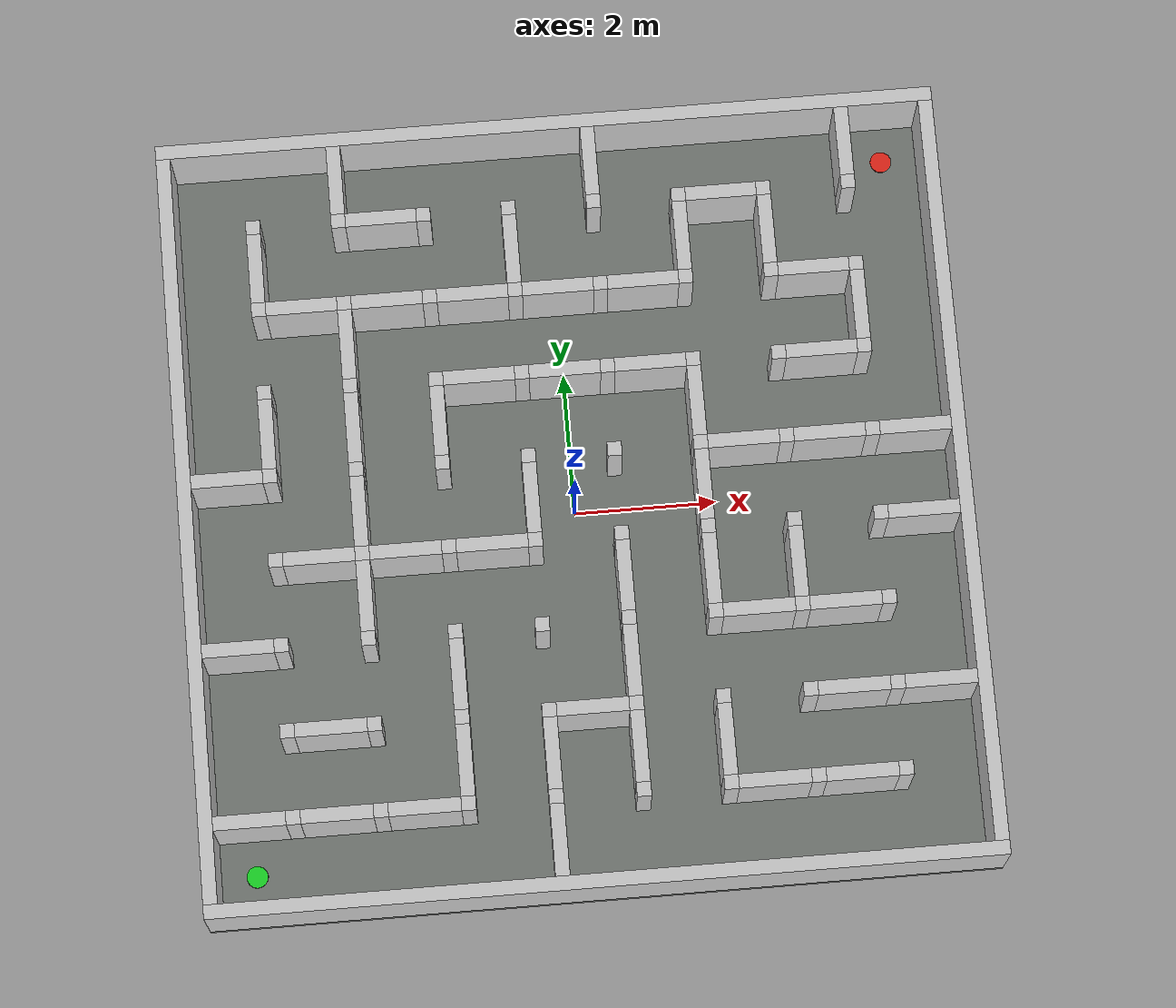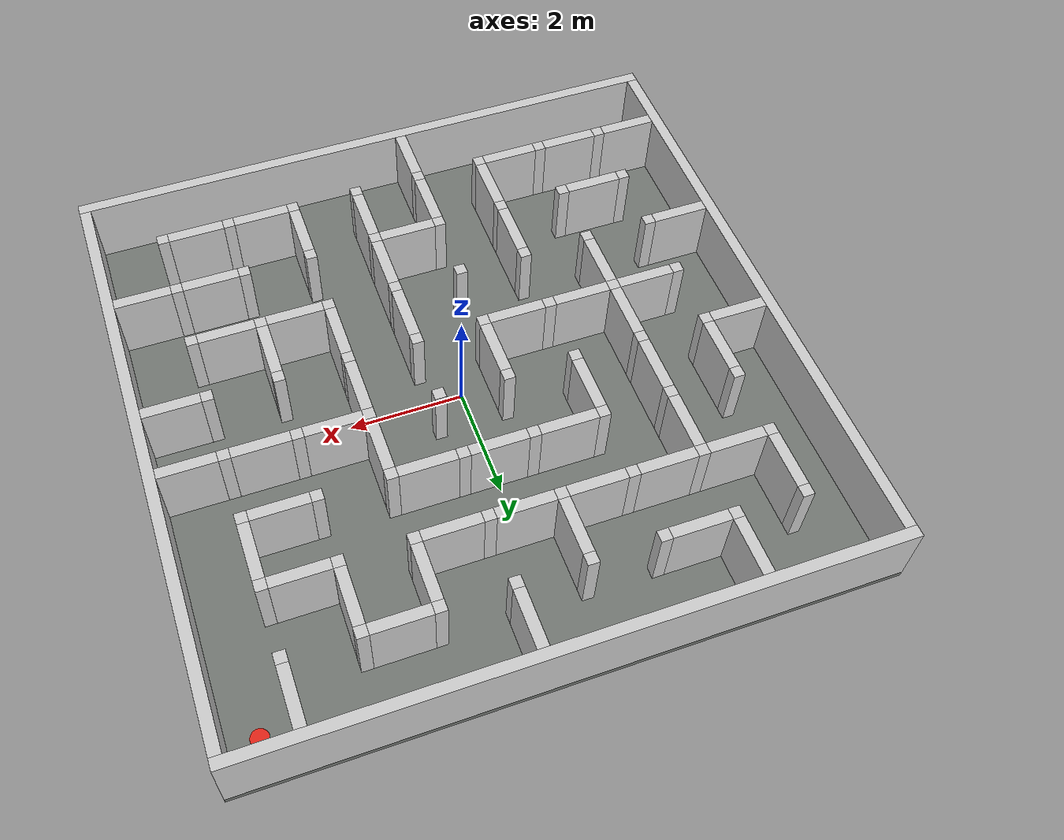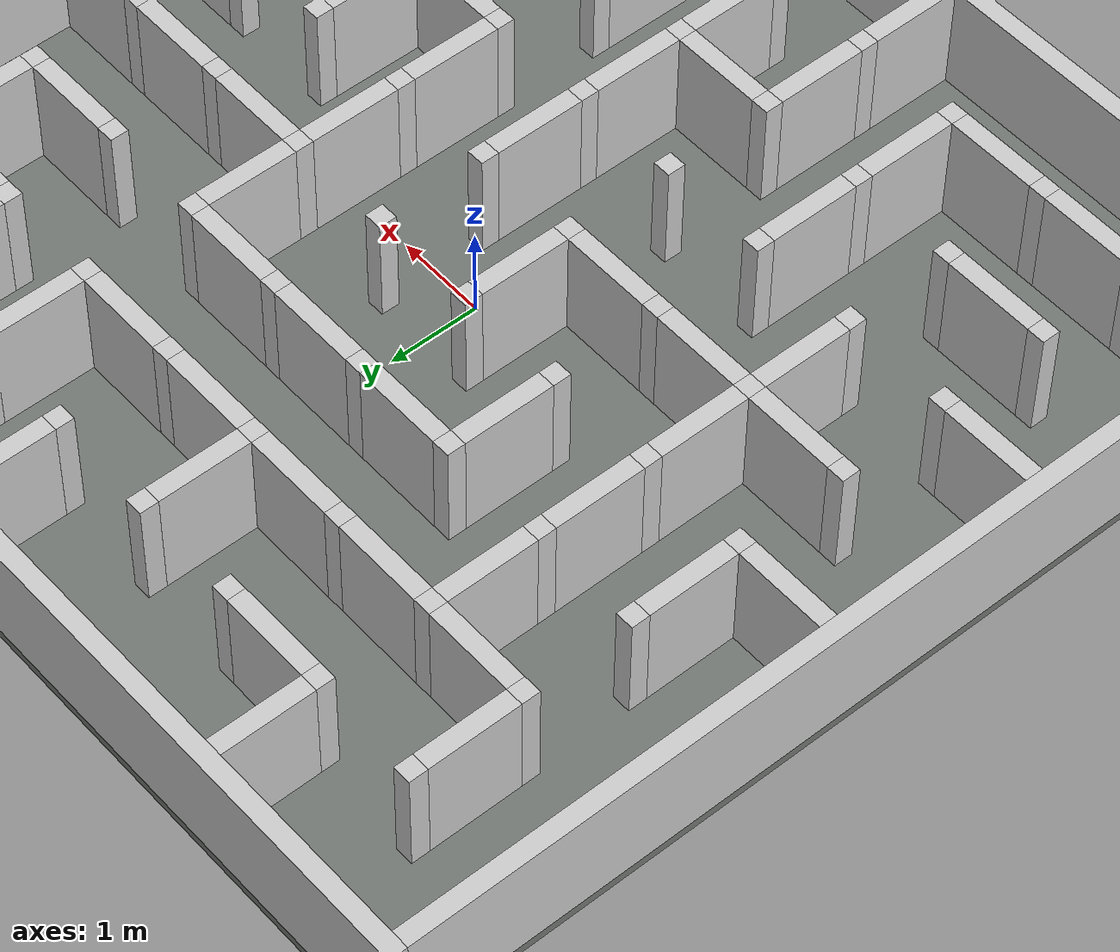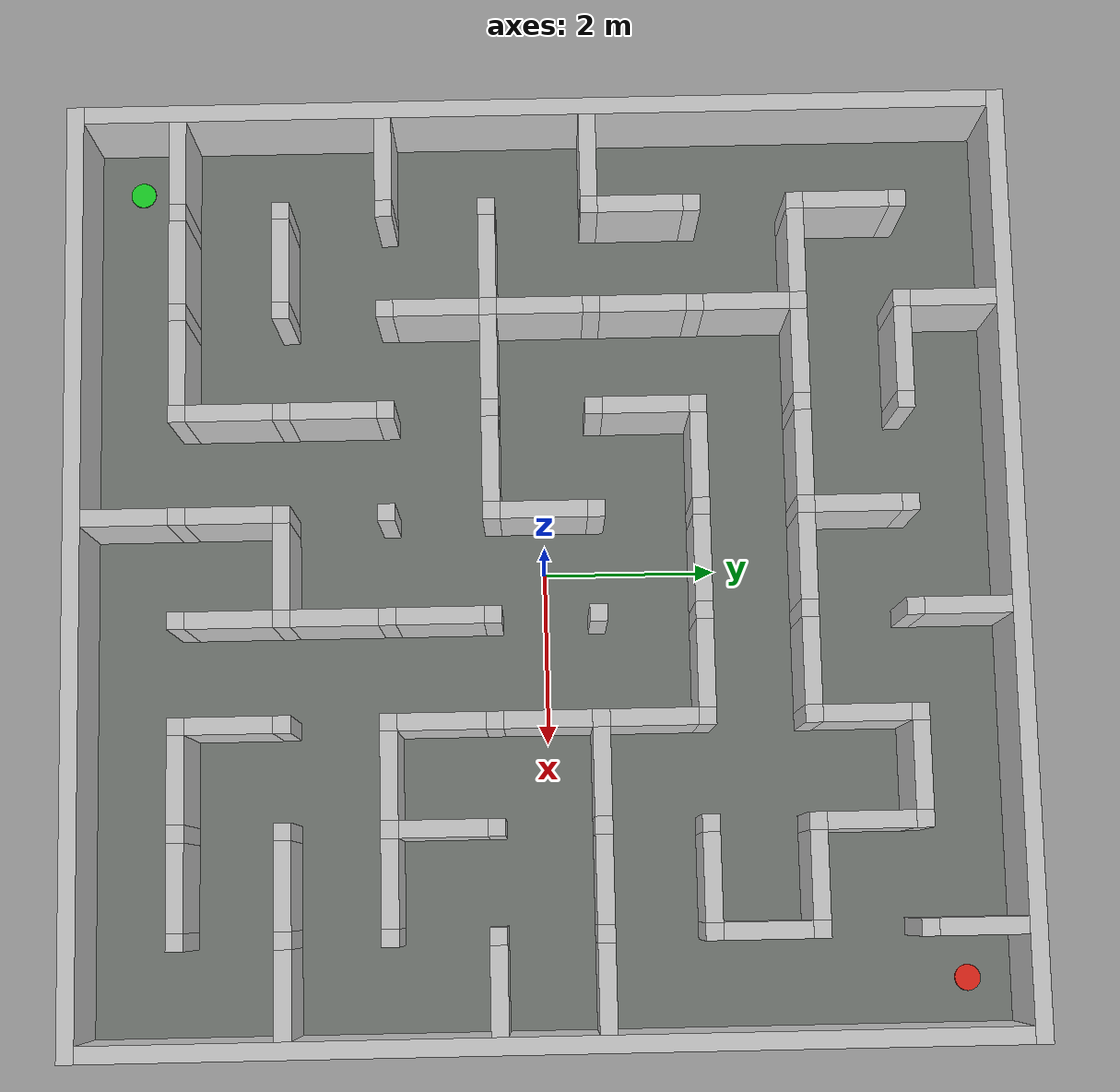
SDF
<?xml version="1.0"?>
<sdf version="1.9">
  <world name="maze">
    <!--
      物理引擎与步长。type=dart 使用 DART 引擎；max_step_size=0.001
      表示每个物理步长 1ms，real_time_update_rate=1000 表示每实秒计算
      1000 步（即实时比约 1:1）。步长取小是为了让薄墙碰撞更稳定。
    -->
    <physics name="1ms" type="dart">
      <max_step_size>0.001</max_step_size>
      <real_time_update_rate>1000</real_time_update_rate>
    </physics>

    <!--
      以下四个是 gz-sim 的系统插件，决定“仿真本身怎么运转”：
      Physics 负责动力学解算；UserCommands 处理运行时插入/删除实体
      （maze_bot 的 spawn 就靠它）；SceneBroadcaster 对外发布场景状态；
      Sensors 提供传感器渲染管线（相机/雷达依赖它，渲染引擎为 ogre2）。
    -->
    <plugin filename="gz-sim-physics-system" name="gz::sim::systems::Physics"/>
    <plugin filename="gz-sim-user-commands-system"
            name="gz::sim::systems::UserCommands"/>
    <plugin filename="gz-sim-scene-broadcaster-system"
            name="gz::sim::systems::SceneBroadcaster"/>
    <plugin filename="gz-sim-sensors-system" name="gz::sim::systems::Sensors">
      <render_engine>ogre2</render_engine>
    </plugin>

    <gui fullscreen="0">

      <plugin filename="MinimalScene" name="3D View">
          <gz-gui>
              <title>3D View</title>
              <property type="bool" key="showTitleBar">false</property>
              <property type="string" key="state">docked</property>
          </gz-gui>
          <engine>ogre2</engine>
          <scene>scene</scene>
          <ambient_light>0.4 0.4 0.4</ambient_light>
          <background_color>0.8 0.8 0.8</background_color>
          <camera_pose>-6 0 6 0 0.5 0</camera_pose>
      </plugin>

      <plugin filename="EntityContextMenuPlugin" name="Entity context menu">
          <gz-gui>
              <property key="state" type="string">floating</property>
              <property key="width" type="double">5</property>
              <property key="height" type="double">5</property>
              <property key="showTitleBar" type="bool">false</property>
          </gz-gui>
      </plugin>

      <plugin filename="GzSceneManager" name="Scene Manager">
          <gz-gui>
              <property key="resizable" type="bool">false</property>
              <property key="width" type="double">5</property>
              <property key="height" type="double">5</property>
              <property key="state" type="string">floating</property>
              <property key="showTitleBar" type="bool">false</property>
          </gz-gui>
      </plugin>

      <plugin filename="InteractiveViewControl" name="Interactive view control">
          <gz-gui>
              <property key="resizable" type="bool">false</property>
              <property key="width" type="double">5</property>
              <property key="height" type="double">5</property>
              <property key="state" type="string">floating</property>
              <property key="showTitleBar" type="bool">false</property>
          </gz-gui>
      </plugin>

      <plugin filename="CameraTracking" name="Camera Tracking">
          <gz-gui>
              <property key="resizable" type="bool">false</property>
              <property key="width" type="double">5</property>
              <property key="height" type="double">5</property>
              <property key="state" type="string">floating</property>
              <property key="showTitleBar" type="bool">false</property>
          </gz-gui>
      </plugin>

      <plugin filename="MarkerManager" name="Marker manager">
          <gz-gui>
              <property key="resizable" type="bool">false</property>
              <property key="width" type="double">5</property>
              <property key="height" type="double">5</property>
              <property key="state" type="string">floating</property>
              <property key="showTitleBar" type="bool">false</property>
          </gz-gui>
      </plugin>

      <plugin filename="SelectEntities" name="Select Entities">
          <gz-gui>
              <property key="resizable" type="bool">false</property>
              <property key="width" type="double">5</property>
              <property key="height" type="double">5</property>
              <property key="state" type="string">floating</property>
              <property key="showTitleBar" type="bool">false</property>
          </gz-gui>
      </plugin>

      <plugin filename="Spawn" name="Spawn Entities">
          <gz-gui>
              <property key="resizable" type="bool">false</property>
              <property key="width" type="double">5</property>
              <property key="height" type="double">5</property>
              <property key="state" type="string">floating</property>
              <property key="showTitleBar" type="bool">false</property>
          </gz-gui>
      </plugin>

      <plugin filename="VisualizationCapabilities" name="Visualization Capabilities">
          <gz-gui>
              <property key="resizable" type="bool">false</property>
              <property key="width" type="double">5</property>
              <property key="height" type="double">5</property>
              <property key="state" type="string">floating</property>
              <property key="showTitleBar" type="bool">false</property>
          </gz-gui>
      </plugin>

      <plugin filename="WorldControl" name="World control">
          <gz-gui>
              <title>World control</title>
              <property type="bool" key="showTitleBar">false</property>
              <property type="bool" key="resizable">false</property>
              <property type="double" key="height">72</property>
              <property type="double" key="z">1</property>
              <property type="string" key="state">floating</property>
              <anchors target="3D View">
                  <line own="left" target="left"/>
                  <line own="bottom" target="bottom"/>
              </anchors>
          </gz-gui>
          <play_pause>true</play_pause>
          <step>true</step>
          <start_paused>true</start_paused>
          <use_event>true</use_event>
      </plugin>

      <plugin filename="WorldStats" name="World stats">
          <gz-gui>
              <title>World stats</title>
              <property type="bool" key="showTitleBar">false</property>
              <property type="bool" key="resizable">false</property>
              <property type="double" key="height">110</property>
              <property type="double" key="width">290</property>
              <property type="double" key="z">1</property>
              <property type="string" key="state">floating</property>
              <anchors target="3D View">
                  <line own="right" target="right"/>
                  <line own="bottom" target="bottom"/>
              </anchors>
          </gz-gui>
          <sim_time>true</sim_time>
          <real_time>true</real_time>
          <real_time_factor>true</real_time_factor>
          <iterations>true</iterations>
      </plugin>

      <plugin filename="Shapes" name="Shapes">
          <gz-gui>
              <property key="resizable" type="bool">false</property>
              <property key="x" type="double">0</property>
              <property key="y" type="double">0</property>
              <property key="width" type="double">300</property>
              <property key="height" type="double">50</property>
              <property key="state" type="string">floating</property>
              <property key="showTitleBar" type="bool">false</property>
              <property key="cardBackground" type="string">#666666</property>
          </gz-gui>
      </plugin>

      <plugin filename="Lights" name="Lights">
          <gz-gui>
              <property key="resizable" type="bool">false</property>
              <property key="x" type="double">300</property>
              <property key="y" type="double">0</property>
              <property key="width" type="double">150</property>
              <property key="height" type="double">50</property>
              <property key="state" type="string">floating</property>
              <property key="showTitleBar" type="bool">false</property>
              <property key="cardBackground" type="string">#666666</property>
          </gz-gui>
      </plugin>

      <plugin filename="TransformControl" name="Transform control">
          <gz-gui>
              <property key="resizable" type="bool">false</property>
              <property key="x" type="double">0</property>
              <property key="y" type="double">50</property>
              <property key="width" type="double">250</property>
              <property key="height" type="double">50</property>
              <property key="state" type="string">floating</property>
              <property key="showTitleBar" type="bool">false</property>
              <property key="cardBackground" type="string">#777777</property>
          </gz-gui>
      </plugin>

      <plugin filename="Screenshot" name="Screenshot">
          <gz-gui>
              <property key="resizable" type="bool">false</property>
              <property key="x" type="double">250</property>
              <property key="y" type="double">50</property>
              <property key="width" type="double">50</property>
              <property key="height" type="double">50</property>
              <property key="state" type="string">floating</property>
              <property key="showTitleBar" type="bool">false</property>
              <property key="cardBackground" type="string">#777777</property>
          </gz-gui>
      </plugin>

      <plugin filename="CopyPaste" name="CopyPaste">
          <gz-gui>
              <property key="resizable" type="bool">false</property>
              <property key="x" type="double">300</property>
              <property key="y" type="double">50</property>
              <property key="width" type="double">100</property>
              <property key="height" type="double">50</property>
              <property key="state" type="string">floating</property>
              <property key="showTitleBar" type="bool">false</property>
              <property key="cardBackground" type="string">#777777</property>
          </gz-gui>
      </plugin>

      <plugin filename="ComponentInspector" name="Component inspector">
          <gz-gui>
              <property type="bool" key="showTitleBar">false</property>
              <property type="string" key="state">docked</property>
          </gz-gui>
      </plugin>

      <plugin filename="EntityTree" name="Entity tree">
          <gz-gui>
              <property type="bool" key="showTitleBar">false</property>
              <property type="string" key="state">docked</property>
          </gz-gui>
      </plugin>

      <plugin filename="VisualizeLidar" name="Visualize Lidar">
          <gz-gui>
              <title>Visualize Lidar</title>
              <property type="bool" key="showTitleBar">true</property>
              <property type="string" key="state">docked</property>
          </gz-gui>
      </plugin>
    </gui>

    <!--
      地面。collision 用 100x100 的无限大平面（法线朝上，位于 z=0）；
      visual 则是一个 11x11、厚 0.1 的方块，下移 0.05 使顶面正好在 z=0，
      其边长 = 迷宫跨度 9.6m + 两侧各半个格子 0.5m + 两侧外墙厚 0.2m，
      刚好把迷宫及其外墙完全覆盖，避免看到地面的“边界”。
    -->
    <model name="ground_plane">
      <static>true</static>
      <link name="link">
        <collision name="collision">
          <pose>0 0 0 0 0 0</pose>
          <geometry>
            <plane>
              <normal>0 0 1</normal>
              <size>100 100</size>
            </plane>
          </geometry>
        </collision>
        <visual name="visual">
          <pose>0 0 -0.05 0 0 0</pose>
          <geometry>
            <box>
              <size>11.000 11.000 0.1</size>
            </box>
          </geometry>
          <material>
            <ambient>0.45 0.47 0.45 1</ambient>
            <diffuse>0.45 0.47 0.45 1</diffuse>
            <specular>0.1 0.1 0.1 1</specular>
          </material>
        </visual>
      </link>
    </model>

    <model name="maze_walls">
      <static>true</static>
      <pose>-4.800 -4.800 0 0 0 0</pose>
      <link name="walls">
        <!-- 四面外墙：绕迷宫一圈，长度含两侧外扩量 -->
        <collision name='outer_south_collision'>
          <pose>4.800 -0.600 0.600 0 0 0</pose>
          <geometry>
            <box>
              <size>11.000 0.200 1.200</size>
            </box>
          </geometry>
        </collision>
        <visual name='outer_south_visual'>
          <pose>4.800 -0.600 0.600 0 0 0</pose>
          <geometry>
            <box>
              <size>11.000 0.200 1.200</size>
            </box>
          </geometry>
          <material>
            <ambient>0.55 0.55 0.55 1</ambient>
            <diffuse>0.80 0.80 0.80 1</diffuse>
            <specular>0.1 0.1 0.1 1</specular>
          </material>
        </visual>
        <collision name='outer_north_collision'>
          <pose>4.800 10.200 0.600 0 0 0</pose>
          <geometry>
            <box>
              <size>11.000 0.200 1.200</size>
            </box>
          </geometry>
        </collision>
        <visual name='outer_north_visual'>
          <pose>4.800 10.200 0.600 0 0 0</pose>
          <geometry>
            <box>
              <size>11.000 0.200 1.200</size>
            </box>
          </geometry>
          <material>
            <ambient>0.55 0.55 0.55 1</ambient>
            <diffuse>0.80 0.80 0.80 1</diffuse>
            <specular>0.1 0.1 0.1 1</specular>
          </material>
        </visual>
        <collision name='outer_west_collision'>
          <pose>-0.600 4.800 0.600 0 0 0</pose>
          <geometry>
            <box>
              <size>0.200 10.600 1.200</size>
            </box>
          </geometry>
        </collision>
        <visual name='outer_west_visual'>
          <pose>-0.600 4.800 0.600 0 0 0</pose>
          <geometry>
            <box>
              <size>0.200 10.600 1.200</size>
            </box>
          </geometry>
          <material>
            <ambient>0.55 0.55 0.55 1</ambient>
            <diffuse>0.80 0.80 0.80 1</diffuse>
            <specular>0.1 0.1 0.1 1</specular>
          </material>
        </visual>
        <collision name='outer_east_collision'>
          <pose>10.200 4.800 0.600 0 0 0</pose>
          <geometry>
            <box>
              <size>0.200 10.600 1.200</size>
            </box>
          </geometry>
        </collision>
        <visual name='outer_east_visual'>
          <pose>10.200 4.800 0.600 0 0 0</pose>
          <geometry>
            <box>
              <size>0.200 10.600 1.200</size>
            </box>
          </geometry>
          <material>
            <ambient>0.55 0.55 0.55 1</ambient>
            <diffuse>0.80 0.80 0.80 1</diffuse>
            <specular>0.1 0.1 0.1 1</specular>
          </material>
        </visual>
        <!-- 柱子：8x8 个墙交汇点各放一个 0.2x0.2 的方柱，供墙段连接 -->
        <collision name='pillar_0_0_collision'>
          <pose>0.600 0.600 0.600 0 0 0</pose>
          <geometry>
            <box>
              <size>0.200 0.200 1.200</size>
            </box>
          </geometry>
        </collision>
        <visual name='pillar_0_0_visual'>
          <pose>0.600 0.600 0.600 0 0 0</pose>
          <geometry>
            <box>
              <size>0.200 0.200 1.200</size>
            </box>
          </geometry>
          <material>
            <ambient>0.55 0.55 0.55 1</ambient>
            <diffuse>0.80 0.80 0.80 1</diffuse>
            <specular>0.1 0.1 0.1 1</specular>
          </material>
        </visual>
        <collision name='pillar_0_1_collision'>
          <pose>0.600 1.800 0.600 0 0 0</pose>
          <geometry>
            <box>
              <size>0.200 0.200 1.200</size>
            </box>
          </geometry>
        </collision>
        <visual name='pillar_0_1_visual'>
          <pose>0.600 1.800 0.600 0 0 0</pose>
          <geometry>
            <box>
              <size>0.200 0.200 1.200</size>
            </box>
          </geometry>
          <material>
            <ambient>0.55 0.55 0.55 1</ambient>
            <diffuse>0.80 0.80 0.80 1</diffuse>
            <specular>0.1 0.1 0.1 1</specular>
          </material>
        </visual>
        <collision name='pillar_0_2_collision'>
          <pose>0.600 3.000 0.600 0 0 0</pose>
          <geometry>
            <box>
              <size>0.200 0.200 1.200</size>
            </box>
          </geometry>
        </collision>
        <visual name='pillar_0_2_visual'>
          <pose>0.600 3.000 0.600 0 0 0</pose>
          <geometry>
            <box>
              <size>0.200 0.200 1.200</size>
            </box>
          </geometry>
          <material>
            <ambient>0.55 0.55 0.55 1</ambient>
            <diffuse>0.80 0.80 0.80 1</diffuse>
            <specular>0.1 0.1 0.1 1</specular>
          </material>
        </visual>
        <collision name='pillar_0_3_collision'>
          <pose>0.600 4.200 0.600 0 0 0</pose>
          <geometry>
            <box>
              <size>0.200 0.200 1.200</size>
            </box>
          </geometry>
        </collision>
        <visual name='pillar_0_3_visual'>
          <pose>0.600 4.200 0.600 0 0 0</pose>
          <geometry>
            <box>
              <size>0.200 0.200 1.200</size>
            </box>
          </geometry>
          <material>
            <ambient>0.55 0.55 0.55 1</ambient>
            <diffuse>0.80 0.80 0.80 1</diffuse>
            <specular>0.1 0.1 0.1 1</specular>
          </material>
        </visual>
        <collision name='pillar_0_4_collision'>
          <pose>0.600 5.400 0.600 0 0 0</pose>
          <geometry>
            <box>
              <size>0.200 0.200 1.200</size>
            </box>
          </geometry>
        </collision>
        <visual name='pillar_0_4_visual'>
          <pose>0.600 5.400 0.600 0 0 0</pose>
          <geometry>
            <box>
              <size>0.200 0.200 1.200</size>
            </box>
          </geometry>
          <material>
            <ambient>0.55 0.55 0.55 1</ambient>
            <diffuse>0.80 0.80 0.80 1</diffuse>
            <specular>0.1 0.1 0.1 1</specular>
          </material>
        </visual>
        <collision name='pillar_0_5_collision'>
          <pose>0.600 6.600 0.600 0 0 0</pose>
          <geometry>
            <box>
              <size>0.200 0.200 1.200</size>
            </box>
          </geometry>
        </collision>
        <visual name='pillar_0_5_visual'>
          <pose>0.600 6.600 0.600 0 0 0</pose>
          <geometry>
            <box>
              <size>0.200 0.200 1.200</size>
            </box>
          </geometry>
          <material>
            <ambient>0.55 0.55 0.55 1</ambient>
            <diffuse>0.80 0.80 0.80 1</diffuse>
            <specular>0.1 0.1 0.1 1</specular>
          </material>
        </visual>
        <collision name='pillar_0_6_collision'>
          <pose>0.600 7.800 0.600 0 0 0</pose>
          <geometry>
            <box>
              <size>0.200 0.200 1.200</size>
            </box>
          </geometry>
        </collision>
        <visual name='pillar_0_6_visual'>
          <pose>0.600 7.800 0.600 0 0 0</pose>
          <geometry>
            <box>
              <size>0.200 0.200 1.200</size>
            </box>
          </geometry>
          <material>
            <ambient>0.55 0.55 0.55 1</ambient>
            <diffuse>0.80 0.80 0.80 1</diffuse>
            <specular>0.1 0.1 0.1 1</specular>
          </material>
        </visual>
        <collision name='pillar_0_7_collision'>
          <pose>0.600 9.000 0.600 0 0 0</pose>
          <geometry>
            <box>
              <size>0.200 0.200 1.200</size>
            </box>
          </geometry>
        </collision>
        <visual name='pillar_0_7_visual'>
          <pose>0.600 9.000 0.600 0 0 0</pose>
          <geometry>
            <box>
              <size>0.200 0.200 1.200</size>
            </box>
          </geometry>
          <material>
            <ambient>0.55 0.55 0.55 1</ambient>
            <diffuse>0.80 0.80 0.80 1</diffuse>
            <specular>0.1 0.1 0.1 1</specular>
          </material>
        </visual>
        <collision name='pillar_1_0_collision'>
          <pose>1.800 0.600 0.600 0 0 0</pose>
          <geometry>
            <box>
              <size>0.200 0.200 1.200</size>
            </box>
          </geometry>
        </collision>
        <visual name='pillar_1_0_visual'>
          <pose>1.800 0.600 0.600 0 0 0</pose>
          <geometry>
            <box>
              <size>0.200 0.200 1.200</size>
            </box>
          </geometry>
          <material>
            <ambient>0.55 0.55 0.55 1</ambient>
            <diffuse>0.80 0.80 0.80 1</diffuse>
            <specular>0.1 0.1 0.1 1</specular>
          </material>
        </visual>
        <collision name='pillar_1_1_collision'>
          <pose>1.800 1.800 0.600 0 0 0</pose>
          <geometry>
            <box>
              <size>0.200 0.200 1.200</size>
            </box>
          </geometry>
        </collision>
        <visual name='pillar_1_1_visual'>
          <pose>1.800 1.800 0.600 0 0 0</pose>
          <geometry>
            <box>
              <size>0.200 0.200 1.200</size>
            </box>
          </geometry>
          <material>
            <ambient>0.55 0.55 0.55 1</ambient>
            <diffuse>0.80 0.80 0.80 1</diffuse>
            <specular>0.1 0.1 0.1 1</specular>
          </material>
        </visual>
        <collision name='pillar_1_2_collision'>
          <pose>1.800 3.000 0.600 0 0 0</pose>
          <geometry>
            <box>
              <size>0.200 0.200 1.200</size>
            </box>
          </geometry>
        </collision>
        <visual name='pillar_1_2_visual'>
          <pose>1.800 3.000 0.600 0 0 0</pose>
          <geometry>
            <box>
              <size>0.200 0.200 1.200</size>
            </box>
          </geometry>
          <material>
            <ambient>0.55 0.55 0.55 1</ambient>
            <diffuse>0.80 0.80 0.80 1</diffuse>
            <specular>0.1 0.1 0.1 1</specular>
          </material>
        </visual>
        <collision name='pillar_1_3_collision'>
          <pose>1.800 4.200 0.600 0 0 0</pose>
          <geometry>
            <box>
              <size>0.200 0.200 1.200</size>
            </box>
          </geometry>
        </collision>
        <visual name='pillar_1_3_visual'>
          <pose>1.800 4.200 0.600 0 0 0</pose>
          <geometry>
            <box>
              <size>0.200 0.200 1.200</size>
            </box>
          </geometry>
          <material>
            <ambient>0.55 0.55 0.55 1</ambient>
            <diffuse>0.80 0.80 0.80 1</diffuse>
            <specular>0.1 0.1 0.1 1</specular>
          </material>
        </visual>
        <collision name='pillar_1_4_collision'>
          <pose>1.800 5.400 0.600 0 0 0</pose>
          <geometry>
            <box>
              <size>0.200 0.200 1.200</size>
            </box>
          </geometry>
        </collision>
        <visual name='pillar_1_4_visual'>
          <pose>1.800 5.400 0.600 0 0 0</pose>
          <geometry>
            <box>
              <size>0.200 0.200 1.200</size>
            </box>
          </geometry>
          <material>
            <ambient>0.55 0.55 0.55 1</ambient>
            <diffuse>0.80 0.80 0.80 1</diffuse>
            <specular>0.1 0.1 0.1 1</specular>
          </material>
        </visual>
        <collision name='pillar_1_5_collision'>
          <pose>1.800 6.600 0.600 0 0 0</pose>
          <geometry>
            <box>
              <size>0.200 0.200 1.200</size>
            </box>
          </geometry>
        </collision>
        <visual name='pillar_1_5_visual'>
          <pose>1.800 6.600 0.600 0 0 0</pose>
          <geometry>
            <box>
              <size>0.200 0.200 1.200</size>
            </box>
          </geometry>
          <material>
            <ambient>0.55 0.55 0.55 1</ambient>
            <diffuse>0.80 0.80 0.80 1</diffuse>
            <specular>0.1 0.1 0.1 1</specular>
          </material>
        </visual>
        <collision name='pillar_1_6_collision'>
          <pose>1.800 7.800 0.600 0 0 0</pose>
          <geometry>
            <box>
              <size>0.200 0.200 1.200</size>
            </box>
          </geometry>
        </collision>
        <visual name='pillar_1_6_visual'>
          <pose>1.800 7.800 0.600 0 0 0</pose>
          <geometry>
            <box>
              <size>0.200 0.200 1.200</size>
            </box>
          </geometry>
          <material>
            <ambient>0.55 0.55 0.55 1</ambient>
            <diffuse>0.80 0.80 0.80 1</diffuse>
            <specular>0.1 0.1 0.1 1</specular>
          </material>
        </visual>
        <collision name='pillar_1_7_collision'>
          <pose>1.800 9.000 0.600 0 0 0</pose>
          <geometry>
            <box>
              <size>0.200 0.200 1.200</size>
            </box>
          </geometry>
        </collision>
        <visual name='pillar_1_7_visual'>
          <pose>1.800 9.000 0.600 0 0 0</pose>
          <geometry>
            <box>
              <size>0.200 0.200 1.200</size>
            </box>
          </geometry>
          <material>
            <ambient>0.55 0.55 0.55 1</ambient>
            <diffuse>0.80 0.80 0.80 1</diffuse>
            <specular>0.1 0.1 0.1 1</specular>
          </material>
        </visual>
        <collision name='pillar_2_0_collision'>
          <pose>3.000 0.600 0.600 0 0 0</pose>
          <geometry>
            <box>
              <size>0.200 0.200 1.200</size>
            </box>
          </geometry>
        </collision>
        <visual name='pillar_2_0_visual'>
          <pose>3.000 0.600 0.600 0 0 0</pose>
          <geometry>
            <box>
              <size>0.200 0.200 1.200</size>
            </box>
          </geometry>
          <material>
            <ambient>0.55 0.55 0.55 1</ambient>
            <diffuse>0.80 0.80 0.80 1</diffuse>
            <specular>0.1 0.1 0.1 1</specular>
          </material>
        </visual>
        <collision name='pillar_2_1_collision'>
          <pose>3.000 1.800 0.600 0 0 0</pose>
          <geometry>
            <box>
              <size>0.200 0.200 1.200</size>
            </box>
          </geometry>
        </collision>
        <visual name='pillar_2_1_visual'>
          <pose>3.000 1.800 0.600 0 0 0</pose>
          <geometry>
            <box>
              <size>0.200 0.200 1.200</size>
            </box>
          </geometry>
          <material>
            <ambient>0.55 0.55 0.55 1</ambient>
            <diffuse>0.80 0.80 0.80 1</diffuse>
            <specular>0.1 0.1 0.1 1</specular>
          </material>
        </visual>
        <collision name='pillar_2_2_collision'>
          <pose>3.000 3.000 0.600 0 0 0</pose>
          <geometry>
            <box>
              <size>0.200 0.200 1.200</size>
            </box>
          </geometry>
        </collision>
        <visual name='pillar_2_2_visual'>
          <pose>3.000 3.000 0.600 0 0 0</pose>
          <geometry>
            <box>
              <size>0.200 0.200 1.200</size>
            </box>
          </geometry>
          <material>
            <ambient>0.55 0.55 0.55 1</ambient>
            <diffuse>0.80 0.80 0.80 1</diffuse>
            <specular>0.1 0.1 0.1 1</specular>
          </material>
        </visual>
        <collision name='pillar_2_3_collision'>
          <pose>3.000 4.200 0.600 0 0 0</pose>
          <geometry>
            <box>
              <size>0.200 0.200 1.200</size>
            </box>
          </geometry>
        </collision>
        <visual name='pillar_2_3_visual'>
          <pose>3.000 4.200 0.600 0 0 0</pose>
          <geometry>
            <box>
              <size>0.200 0.200 1.200</size>
            </box>
          </geometry>
          <material>
            <ambient>0.55 0.55 0.55 1</ambient>
            <diffuse>0.80 0.80 0.80 1</diffuse>
            <specular>0.1 0.1 0.1 1</specular>
          </material>
        </visual>
        <collision name='pillar_2_4_collision'>
          <pose>3.000 5.400 0.600 0 0 0</pose>
          <geometry>
            <box>
              <size>0.200 0.200 1.200</size>
            </box>
          </geometry>
        </collision>
        <visual name='pillar_2_4_visual'>
          <pose>3.000 5.400 0.600 0 0 0</pose>
          <geometry>
            <box>
              <size>0.200 0.200 1.200</size>
            </box>
          </geometry>
          <material>
            <ambient>0.55 0.55 0.55 1</ambient>
            <diffuse>0.80 0.80 0.80 1</diffuse>
            <specular>0.1 0.1 0.1 1</specular>
          </material>
        </visual>
        <collision name='pillar_2_5_collision'>
          <pose>3.000 6.600 0.600 0 0 0</pose>
          <geometry>
            <box>
              <size>0.200 0.200 1.200</size>
            </box>
          </geometry>
        </collision>
        <visual name='pillar_2_5_visual'>
          <pose>3.000 6.600 0.600 0 0 0</pose>
          <geometry>
            <box>
              <size>0.200 0.200 1.200</size>
            </box>
          </geometry>
          <material>
            <ambient>0.55 0.55 0.55 1</ambient>
            <diffuse>0.80 0.80 0.80 1</diffuse>
            <specular>0.1 0.1 0.1 1</specular>
          </material>
        </visual>
        <collision name='pillar_2_6_collision'>
          <pose>3.000 7.800 0.600 0 0 0</pose>
          <geometry>
            <box>
              <size>0.200 0.200 1.200</size>
            </box>
          </geometry>
        </collision>
        <visual name='pillar_2_6_visual'>
          <pose>3.000 7.800 0.600 0 0 0</pose>
          <geometry>
            <box>
              <size>0.200 0.200 1.200</size>
            </box>
          </geometry>
          <material>
            <ambient>0.55 0.55 0.55 1</ambient>
            <diffuse>0.80 0.80 0.80 1</diffuse>
            <specular>0.1 0.1 0.1 1</specular>
          </material>
        </visual>
        <collision name='pillar_2_7_collision'>
          <pose>3.000 9.000 0.600 0 0 0</pose>
          <geometry>
            <box>
              <size>0.200 0.200 1.200</size>
            </box>
          </geometry>
        </collision>
        <visual name='pillar_2_7_visual'>
          <pose>3.000 9.000 0.600 0 0 0</pose>
          <geometry>
            <box>
              <size>0.200 0.200 1.200</size>
            </box>
          </geometry>
          <material>
            <ambient>0.55 0.55 0.55 1</ambient>
            <diffuse>0.80 0.80 0.80 1</diffuse>
            <specular>0.1 0.1 0.1 1</specular>
          </material>
        </visual>
        <collision name='pillar_3_0_collision'>
          <pose>4.200 0.600 0.600 0 0 0</pose>
          <geometry>
            <box>
              <size>0.200 0.200 1.200</size>
            </box>
          </geometry>
        </collision>
        <visual name='pillar_3_0_visual'>
          <pose>4.200 0.600 0.600 0 0 0</pose>
          <geometry>
            <box>
              <size>0.200 0.200 1.200</size>
            </box>
          </geometry>
          <material>
            <ambient>0.55 0.55 0.55 1</ambient>
            <diffuse>0.80 0.80 0.80 1</diffuse>
            <specular>0.1 0.1 0.1 1</specular>
          </material>
        </visual>
        <collision name='pillar_3_1_collision'>
          <pose>4.200 1.800 0.600 0 0 0</pose>
          <geometry>
            <box>
              <size>0.200 0.200 1.200</size>
            </box>
          </geometry>
        </collision>
        <visual name='pillar_3_1_visual'>
          <pose>4.200 1.800 0.600 0 0 0</pose>
          <geometry>
            <box>
              <size>0.200 0.200 1.200</size>
            </box>
          </geometry>
          <material>
            <ambient>0.55 0.55 0.55 1</ambient>
            <diffuse>0.80 0.80 0.80 1</diffuse>
            <specular>0.1 0.1 0.1 1</specular>
          </material>
        </visual>
        <collision name='pillar_3_2_collision'>
          <pose>4.200 3.000 0.600 0 0 0</pose>
          <geometry>
            <box>
              <size>0.200 0.200 1.200</size>
            </box>
          </geometry>
        </collision>
        <visual name='pillar_3_2_visual'>
          <pose>4.200 3.000 0.600 0 0 0</pose>
          <geometry>
            <box>
              <size>0.200 0.200 1.200</size>
            </box>
          </geometry>
          <material>
            <ambient>0.55 0.55 0.55 1</ambient>
            <diffuse>0.80 0.80 0.80 1</diffuse>
            <specular>0.1 0.1 0.1 1</specular>
          </material>
        </visual>
        <collision name='pillar_3_3_collision'>
          <pose>4.200 4.200 0.600 0 0 0</pose>
          <geometry>
            <box>
              <size>0.200 0.200 1.200</size>
            </box>
          </geometry>
        </collision>
        <visual name='pillar_3_3_visual'>
          <pose>4.200 4.200 0.600 0 0 0</pose>
          <geometry>
            <box>
              <size>0.200 0.200 1.200</size>
            </box>
          </geometry>
          <material>
            <ambient>0.55 0.55 0.55 1</ambient>
            <diffuse>0.80 0.80 0.80 1</diffuse>
            <specular>0.1 0.1 0.1 1</specular>
          </material>
        </visual>
        <collision name='pillar_3_4_collision'>
          <pose>4.200 5.400 0.600 0 0 0</pose>
          <geometry>
            <box>
              <size>0.200 0.200 1.200</size>
            </box>
          </geometry>
        </collision>
        <visual name='pillar_3_4_visual'>
          <pose>4.200 5.400 0.600 0 0 0</pose>
          <geometry>
            <box>
              <size>0.200 0.200 1.200</size>
            </box>
          </geometry>
          <material>
            <ambient>0.55 0.55 0.55 1</ambient>
            <diffuse>0.80 0.80 0.80 1</diffuse>
            <specular>0.1 0.1 0.1 1</specular>
          </material>
        </visual>
        <collision name='pillar_3_5_collision'>
          <pose>4.200 6.600 0.600 0 0 0</pose>
          <geometry>
            <box>
              <size>0.200 0.200 1.200</size>
            </box>
          </geometry>
        </collision>
        <visual name='pillar_3_5_visual'>
          <pose>4.200 6.600 0.600 0 0 0</pose>
          <geometry>
            <box>
              <size>0.200 0.200 1.200</size>
            </box>
          </geometry>
          <material>
            <ambient>0.55 0.55 0.55 1</ambient>
            <diffuse>0.80 0.80 0.80 1</diffuse>
            <specular>0.1 0.1 0.1 1</specular>
          </material>
        </visual>
        <collision name='pillar_3_6_collision'>
          <pose>4.200 7.800 0.600 0 0 0</pose>
          <geometry>
            <box>
              <size>0.200 0.200 1.200</size>
            </box>
          </geometry>
        </collision>
        <visual name='pillar_3_6_visual'>
          <pose>4.200 7.800 0.600 0 0 0</pose>
          <geometry>
            <box>
              <size>0.200 0.200 1.200</size>
            </box>
          </geometry>
          <material>
            <ambient>0.55 0.55 0.55 1</ambient>
            <diffuse>0.80 0.80 0.80 1</diffuse>
            <specular>0.1 0.1 0.1 1</specular>
          </material>
        </visual>
        <collision name='pillar_3_7_collision'>
          <pose>4.200 9.000 0.600 0 0 0</pose>
          <geometry>
            <box>
              <size>0.200 0.200 1.200</size>
            </box>
          </geometry>
        </collision>
        <visual name='pillar_3_7_visual'>
          <pose>4.200 9.000 0.600 0 0 0</pose>
          <geometry>
            <box>
              <size>0.200 0.200 1.200</size>
            </box>
          </geometry>
          <material>
            <ambient>0.55 0.55 0.55 1</ambient>
            <diffuse>0.80 0.80 0.80 1</diffuse>
            <specular>0.1 0.1 0.1 1</specular>
          </material>
        </visual>
        <collision name='pillar_4_0_collision'>
          <pose>5.400 0.600 0.600 0 0 0</pose>
          <geometry>
            <box>
              <size>0.200 0.200 1.200</size>
            </box>
          </geometry>
        </collision>
        <visual name='pillar_4_0_visual'>
          <pose>5.400 0.600 0.600 0 0 0</pose>
          <geometry>
            <box>
              <size>0.200 0.200 1.200</size>
            </box>
          </geometry>
          <material>
            <ambient>0.55 0.55 0.55 1</ambient>
            <diffuse>0.80 0.80 0.80 1</diffuse>
            <specular>0.1 0.1 0.1 1</specular>
          </material>
        </visual>
        <collision name='pillar_4_1_collision'>
          <pose>5.400 1.800 0.600 0 0 0</pose>
          <geometry>
            <box>
              <size>0.200 0.200 1.200</size>
            </box>
          </geometry>
        </collision>
        <visual name='pillar_4_1_visual'>
          <pose>5.400 1.800 0.600 0 0 0</pose>
          <geometry>
            <box>
              <size>0.200 0.200 1.200</size>
            </box>
          </geometry>
          <material>
            <ambient>0.55 0.55 0.55 1</ambient>
            <diffuse>0.80 0.80 0.80 1</diffuse>
            <specular>0.1 0.1 0.1 1</specular>
          </material>
        </visual>
        <collision name='pillar_4_2_collision'>
          <pose>5.400 3.000 0.600 0 0 0</pose>
          <geometry>
            <box>
              <size>0.200 0.200 1.200</size>
            </box>
          </geometry>
        </collision>
        <visual name='pillar_4_2_visual'>
          <pose>5.400 3.000 0.600 0 0 0</pose>
          <geometry>
            <box>
              <size>0.200 0.200 1.200</size>
            </box>
          </geometry>
          <material>
            <ambient>0.55 0.55 0.55 1</ambient>
            <diffuse>0.80 0.80 0.80 1</diffuse>
            <specular>0.1 0.1 0.1 1</specular>
          </material>
        </visual>
        <collision name='pillar_4_3_collision'>
          <pose>5.400 4.200 0.600 0 0 0</pose>
          <geometry>
            <box>
              <size>0.200 0.200 1.200</size>
            </box>
          </geometry>
        </collision>
        <visual name='pillar_4_3_visual'>
          <pose>5.400 4.200 0.600 0 0 0</pose>
          <geometry>
            <box>
              <size>0.200 0.200 1.200</size>
            </box>
          </geometry>
          <material>
            <ambient>0.55 0.55 0.55 1</ambient>
            <diffuse>0.80 0.80 0.80 1</diffuse>
            <specular>0.1 0.1 0.1 1</specular>
          </material>
        </visual>
        <collision name='pillar_4_4_collision'>
          <pose>5.400 5.400 0.600 0 0 0</pose>
          <geometry>
            <box>
              <size>0.200 0.200 1.200</size>
            </box>
          </geometry>
        </collision>
        <visual name='pillar_4_4_visual'>
          <pose>5.400 5.400 0.600 0 0 0</pose>
          <geometry>
            <box>
              <size>0.200 0.200 1.200</size>
            </box>
          </geometry>
          <material>
            <ambient>0.55 0.55 0.55 1</ambient>
            <diffuse>0.80 0.80 0.80 1</diffuse>
            <specular>0.1 0.1 0.1 1</specular>
          </material>
        </visual>
        <collision name='pillar_4_5_collision'>
          <pose>5.400 6.600 0.600 0 0 0</pose>
          <geometry>
            <box>
              <size>0.200 0.200 1.200</size>
            </box>
          </geometry>
        </collision>
        <visual name='pillar_4_5_visual'>
          <pose>5.400 6.600 0.600 0 0 0</pose>
          <geometry>
            <box>
              <size>0.200 0.200 1.200</size>
            </box>
          </geometry>
          <material>
            <ambient>0.55 0.55 0.55 1</ambient>
            <diffuse>0.80 0.80 0.80 1</diffuse>
            <specular>0.1 0.1 0.1 1</specular>
          </material>
        </visual>
        <collision name='pillar_4_6_collision'>
          <pose>5.400 7.800 0.600 0 0 0</pose>
          <geometry>
            <box>
              <size>0.200 0.200 1.200</size>
            </box>
          </geometry>
        </collision>
        <visual name='pillar_4_6_visual'>
          <pose>5.400 7.800 0.600 0 0 0</pose>
          <geometry>
            <box>
              <size>0.200 0.200 1.200</size>
            </box>
          </geometry>
          <material>
            <ambient>0.55 0.55 0.55 1</ambient>
            <diffuse>0.80 0.80 0.80 1</diffuse>
            <specular>0.1 0.1 0.1 1</specular>
          </material>
        </visual>
        <collision name='pillar_4_7_collision'>
          <pose>5.400 9.000 0.600 0 0 0</pose>
          <geometry>
            <box>
              <size>0.200 0.200 1.200</size>
            </box>
          </geometry>
        </collision>
        <visual name='pillar_4_7_visual'>
          <pose>5.400 9.000 0.600 0 0 0</pose>
          <geometry>
            <box>
              <size>0.200 0.200 1.200</size>
            </box>
          </geometry>
          <material>
            <ambient>0.55 0.55 0.55 1</ambient>
            <diffuse>0.80 0.80 0.80 1</diffuse>
            <specular>0.1 0.1 0.1 1</specular>
          </material>
        </visual>
        <collision name='pillar_5_0_collision'>
          <pose>6.600 0.600 0.600 0 0 0</pose>
          <geometry>
            <box>
              <size>0.200 0.200 1.200</size>
            </box>
          </geometry>
        </collision>
        <visual name='pillar_5_0_visual'>
          <pose>6.600 0.600 0.600 0 0 0</pose>
          <geometry>
            <box>
              <size>0.200 0.200 1.200</size>
            </box>
          </geometry>
          <material>
            <ambient>0.55 0.55 0.55 1</ambient>
            <diffuse>0.80 0.80 0.80 1</diffuse>
            <specular>0.1 0.1 0.1 1</specular>
          </material>
        </visual>
        <collision name='pillar_5_1_collision'>
          <pose>6.600 1.800 0.600 0 0 0</pose>
          <geometry>
            <box>
              <size>0.200 0.200 1.200</size>
            </box>
          </geometry>
        </collision>
        <visual name='pillar_5_1_visual'>
          <pose>6.600 1.800 0.600 0 0 0</pose>
          <geometry>
            <box>
              <size>0.200 0.200 1.200</size>
            </box>
          </geometry>
          <material>
            <ambient>0.55 0.55 0.55 1</ambient>
            <diffuse>0.80 0.80 0.80 1</diffuse>
            <specular>0.1 0.1 0.1 1</specular>
          </material>
        </visual>
        <collision name='pillar_5_2_collision'>
          <pose>6.600 3.000 0.600 0 0 0</pose>
          <geometry>
            <box>
              <size>0.200 0.200 1.200</size>
            </box>
          </geometry>
        </collision>
        <visual name='pillar_5_2_visual'>
          <pose>6.600 3.000 0.600 0 0 0</pose>
          <geometry>
            <box>
              <size>0.200 0.200 1.200</size>
            </box>
          </geometry>
          <material>
            <ambient>0.55 0.55 0.55 1</ambient>
            <diffuse>0.80 0.80 0.80 1</diffuse>
            <specular>0.1 0.1 0.1 1</specular>
          </material>
        </visual>
        <collision name='pillar_5_3_collision'>
          <pose>6.600 4.200 0.600 0 0 0</pose>
          <geometry>
            <box>
              <size>0.200 0.200 1.200</size>
            </box>
          </geometry>
        </collision>
        <visual name='pillar_5_3_visual'>
          <pose>6.600 4.200 0.600 0 0 0</pose>
          <geometry>
            <box>
              <size>0.200 0.200 1.200</size>
            </box>
          </geometry>
          <material>
            <ambient>0.55 0.55 0.55 1</ambient>
            <diffuse>0.80 0.80 0.80 1</diffuse>
            <specular>0.1 0.1 0.1 1</specular>
          </material>
        </visual>
        <collision name='pillar_5_4_collision'>
          <pose>6.600 5.400 0.600 0 0 0</pose>
          <geometry>
            <box>
              <size>0.200 0.200 1.200</size>
            </box>
          </geometry>
        </collision>
        <visual name='pillar_5_4_visual'>
          <pose>6.600 5.400 0.600 0 0 0</pose>
          <geometry>
            <box>
              <size>0.200 0.200 1.200</size>
            </box>
          </geometry>
          <material>
            <ambient>0.55 0.55 0.55 1</ambient>
            <diffuse>0.80 0.80 0.80 1</diffuse>
            <specular>0.1 0.1 0.1 1</specular>
          </material>
        </visual>
        <collision name='pillar_5_5_collision'>
          <pose>6.600 6.600 0.600 0 0 0</pose>
          <geometry>
            <box>
              <size>0.200 0.200 1.200</size>
            </box>
          </geometry>
        </collision>
        <visual name='pillar_5_5_visual'>
          <pose>6.600 6.600 0.600 0 0 0</pose>
          <geometry>
            <box>
              <size>0.200 0.200 1.200</size>
            </box>
          </geometry>
          <material>
            <ambient>0.55 0.55 0.55 1</ambient>
            <diffuse>0.80 0.80 0.80 1</diffuse>
            <specular>0.1 0.1 0.1 1</specular>
          </material>
        </visual>
        <collision name='pillar_5_6_collision'>
          <pose>6.600 7.800 0.600 0 0 0</pose>
          <geometry>
            <box>
              <size>0.200 0.200 1.200</size>
            </box>
          </geometry>
        </collision>
        <visual name='pillar_5_6_visual'>
          <pose>6.600 7.800 0.600 0 0 0</pose>
          <geometry>
            <box>
              <size>0.200 0.200 1.200</size>
            </box>
          </geometry>
          <material>
            <ambient>0.55 0.55 0.55 1</ambient>
            <diffuse>0.80 0.80 0.80 1</diffuse>
            <specular>0.1 0.1 0.1 1</specular>
          </material>
        </visual>
        <collision name='pillar_5_7_collision'>
          <pose>6.600 9.000 0.600 0 0 0</pose>
          <geometry>
            <box>
              <size>0.200 0.200 1.200</size>
            </box>
          </geometry>
        </collision>
        <visual name='pillar_5_7_visual'>
          <pose>6.600 9.000 0.600 0 0 0</pose>
          <geometry>
            <box>
              <size>0.200 0.200 1.200</size>
            </box>
          </geometry>
          <material>
            <ambient>0.55 0.55 0.55 1</ambient>
            <diffuse>0.80 0.80 0.80 1</diffuse>
            <specular>0.1 0.1 0.1 1</specular>
          </material>
        </visual>
        <collision name='pillar_6_0_collision'>
          <pose>7.800 0.600 0.600 0 0 0</pose>
          <geometry>
            <box>
              <size>0.200 0.200 1.200</size>
            </box>
          </geometry>
        </collision>
        <visual name='pillar_6_0_visual'>
          <pose>7.800 0.600 0.600 0 0 0</pose>
          <geometry>
            <box>
              <size>0.200 0.200 1.200</size>
            </box>
          </geometry>
          <material>
            <ambient>0.55 0.55 0.55 1</ambient>
            <diffuse>0.80 0.80 0.80 1</diffuse>
            <specular>0.1 0.1 0.1 1</specular>
          </material>
        </visual>
        <collision name='pillar_6_1_collision'>
          <pose>7.800 1.800 0.600 0 0 0</pose>
          <geometry>
            <box>
              <size>0.200 0.200 1.200</size>
            </box>
          </geometry>
        </collision>
        <visual name='pillar_6_1_visual'>
          <pose>7.800 1.800 0.600 0 0 0</pose>
          <geometry>
            <box>
              <size>0.200 0.200 1.200</size>
            </box>
          </geometry>
          <material>
            <ambient>0.55 0.55 0.55 1</ambient>
            <diffuse>0.80 0.80 0.80 1</diffuse>
            <specular>0.1 0.1 0.1 1</specular>
          </material>
        </visual>
        <collision name='pillar_6_2_collision'>
          <pose>7.800 3.000 0.600 0 0 0</pose>
          <geometry>
            <box>
              <size>0.200 0.200 1.200</size>
            </box>
          </geometry>
        </collision>
        <visual name='pillar_6_2_visual'>
          <pose>7.800 3.000 0.600 0 0 0</pose>
          <geometry>
            <box>
              <size>0.200 0.200 1.200</size>
            </box>
          </geometry>
          <material>
            <ambient>0.55 0.55 0.55 1</ambient>
            <diffuse>0.80 0.80 0.80 1</diffuse>
            <specular>0.1 0.1 0.1 1</specular>
          </material>
        </visual>
        <collision name='pillar_6_3_collision'>
          <pose>7.800 4.200 0.600 0 0 0</pose>
          <geometry>
            <box>
              <size>0.200 0.200 1.200</size>
            </box>
          </geometry>
        </collision>
        <visual name='pillar_6_3_visual'>
          <pose>7.800 4.200 0.600 0 0 0</pose>
          <geometry>
            <box>
              <size>0.200 0.200 1.200</size>
            </box>
          </geometry>
          <material>
            <ambient>0.55 0.55 0.55 1</ambient>
            <diffuse>0.80 0.80 0.80 1</diffuse>
            <specular>0.1 0.1 0.1 1</specular>
          </material>
        </visual>
        <collision name='pillar_6_4_collision'>
          <pose>7.800 5.400 0.600 0 0 0</pose>
          <geometry>
            <box>
              <size>0.200 0.200 1.200</size>
            </box>
          </geometry>
        </collision>
        <visual name='pillar_6_4_visual'>
          <pose>7.800 5.400 0.600 0 0 0</pose>
          <geometry>
            <box>
              <size>0.200 0.200 1.200</size>
            </box>
          </geometry>
          <material>
            <ambient>0.55 0.55 0.55 1</ambient>
            <diffuse>0.80 0.80 0.80 1</diffuse>
            <specular>0.1 0.1 0.1 1</specular>
          </material>
        </visual>
        <collision name='pillar_6_5_collision'>
          <pose>7.800 6.600 0.600 0 0 0</pose>
          <geometry>
            <box>
              <size>0.200 0.200 1.200</size>
            </box>
          </geometry>
        </collision>
        <visual name='pillar_6_5_visual'>
          <pose>7.800 6.600 0.600 0 0 0</pose>
          <geometry>
            <box>
              <size>0.200 0.200 1.200</size>
            </box>
          </geometry>
          <material>
            <ambient>0.55 0.55 0.55 1</ambient>
            <diffuse>0.80 0.80 0.80 1</diffuse>
            <specular>0.1 0.1 0.1 1</specular>
          </material>
        </visual>
        <collision name='pillar_6_6_collision'>
          <pose>7.800 7.800 0.600 0 0 0</pose>
          <geometry>
            <box>
              <size>0.200 0.200 1.200</size>
            </box>
          </geometry>
        </collision>
        <visual name='pillar_6_6_visual'>
          <pose>7.800 7.800 0.600 0 0 0</pose>
          <geometry>
            <box>
              <size>0.200 0.200 1.200</size>
            </box>
          </geometry>
          <material>
            <ambient>0.55 0.55 0.55 1</ambient>
            <diffuse>0.80 0.80 0.80 1</diffuse>
            <specular>0.1 0.1 0.1 1</specular>
          </material>
        </visual>
        <collision name='pillar_6_7_collision'>
          <pose>7.800 9.000 0.600 0 0 0</pose>
          <geometry>
            <box>
              <size>0.200 0.200 1.200</size>
            </box>
          </geometry>
        </collision>
        <visual name='pillar_6_7_visual'>
          <pose>7.800 9.000 0.600 0 0 0</pose>
          <geometry>
            <box>
              <size>0.200 0.200 1.200</size>
            </box>
          </geometry>
          <material>
            <ambient>0.55 0.55 0.55 1</ambient>
            <diffuse>0.80 0.80 0.80 1</diffuse>
            <specular>0.1 0.1 0.1 1</specular>
          </material>
        </visual>
        <collision name='pillar_7_0_collision'>
          <pose>9.000 0.600 0.600 0 0 0</pose>
          <geometry>
            <box>
              <size>0.200 0.200 1.200</size>
            </box>
          </geometry>
        </collision>
        <visual name='pillar_7_0_visual'>
          <pose>9.000 0.600 0.600 0 0 0</pose>
          <geometry>
            <box>
              <size>0.200 0.200 1.200</size>
            </box>
          </geometry>
          <material>
            <ambient>0.55 0.55 0.55 1</ambient>
            <diffuse>0.80 0.80 0.80 1</diffuse>
            <specular>0.1 0.1 0.1 1</specular>
          </material>
        </visual>
        <collision name='pillar_7_1_collision'>
          <pose>9.000 1.800 0.600 0 0 0</pose>
          <geometry>
            <box>
              <size>0.200 0.200 1.200</size>
            </box>
          </geometry>
        </collision>
        <visual name='pillar_7_1_visual'>
          <pose>9.000 1.800 0.600 0 0 0</pose>
          <geometry>
            <box>
              <size>0.200 0.200 1.200</size>
            </box>
          </geometry>
          <material>
            <ambient>0.55 0.55 0.55 1</ambient>
            <diffuse>0.80 0.80 0.80 1</diffuse>
            <specular>0.1 0.1 0.1 1</specular>
          </material>
        </visual>
        <collision name='pillar_7_2_collision'>
          <pose>9.000 3.000 0.600 0 0 0</pose>
          <geometry>
            <box>
              <size>0.200 0.200 1.200</size>
            </box>
          </geometry>
        </collision>
        <visual name='pillar_7_2_visual'>
          <pose>9.000 3.000 0.600 0 0 0</pose>
          <geometry>
            <box>
              <size>0.200 0.200 1.200</size>
            </box>
          </geometry>
          <material>
            <ambient>0.55 0.55 0.55 1</ambient>
            <diffuse>0.80 0.80 0.80 1</diffuse>
            <specular>0.1 0.1 0.1 1</specular>
          </material>
        </visual>
        <collision name='pillar_7_3_collision'>
          <pose>9.000 4.200 0.600 0 0 0</pose>
          <geometry>
            <box>
              <size>0.200 0.200 1.200</size>
            </box>
          </geometry>
        </collision>
        <visual name='pillar_7_3_visual'>
          <pose>9.000 4.200 0.600 0 0 0</pose>
          <geometry>
            <box>
              <size>0.200 0.200 1.200</size>
            </box>
          </geometry>
          <material>
            <ambient>0.55 0.55 0.55 1</ambient>
            <diffuse>0.80 0.80 0.80 1</diffuse>
            <specular>0.1 0.1 0.1 1</specular>
          </material>
        </visual>
        <collision name='pillar_7_4_collision'>
          <pose>9.000 5.400 0.600 0 0 0</pose>
          <geometry>
            <box>
              <size>0.200 0.200 1.200</size>
            </box>
          </geometry>
        </collision>
        <visual name='pillar_7_4_visual'>
          <pose>9.000 5.400 0.600 0 0 0</pose>
          <geometry>
            <box>
              <size>0.200 0.200 1.200</size>
            </box>
          </geometry>
          <material>
            <ambient>0.55 0.55 0.55 1</ambient>
            <diffuse>0.80 0.80 0.80 1</diffuse>
            <specular>0.1 0.1 0.1 1</specular>
          </material>
        </visual>
        <collision name='pillar_7_5_collision'>
          <pose>9.000 6.600 0.600 0 0 0</pose>
          <geometry>
            <box>
              <size>0.200 0.200 1.200</size>
            </box>
          </geometry>
        </collision>
        <visual name='pillar_7_5_visual'>
          <pose>9.000 6.600 0.600 0 0 0</pose>
          <geometry>
            <box>
              <size>0.200 0.200 1.200</size>
            </box>
          </geometry>
          <material>
            <ambient>0.55 0.55 0.55 1</ambient>
            <diffuse>0.80 0.80 0.80 1</diffuse>
            <specular>0.1 0.1 0.1 1</specular>
          </material>
        </visual>
        <collision name='pillar_7_6_collision'>
          <pose>9.000 7.800 0.600 0 0 0</pose>
          <geometry>
            <box>
              <size>0.200 0.200 1.200</size>
            </box>
          </geometry>
        </collision>
        <visual name='pillar_7_6_visual'>
          <pose>9.000 7.800 0.600 0 0 0</pose>
          <geometry>
            <box>
              <size>0.200 0.200 1.200</size>
            </box>
          </geometry>
          <material>
            <ambient>0.55 0.55 0.55 1</ambient>
            <diffuse>0.80 0.80 0.80 1</diffuse>
            <specular>0.1 0.1 0.1 1</specular>
          </material>
        </visual>
        <collision name='pillar_7_7_collision'>
          <pose>9.000 9.000 0.600 0 0 0</pose>
          <geometry>
            <box>
              <size>0.200 0.200 1.200</size>
            </box>
          </geometry>
        </collision>
        <visual name='pillar_7_7_visual'>
          <pose>9.000 9.000 0.600 0 0 0</pose>
          <geometry>
            <box>
              <size>0.200 0.200 1.200</size>
            </box>
          </geometry>
          <material>
            <ambient>0.55 0.55 0.55 1</ambient>
            <diffuse>0.80 0.80 0.80 1</diffuse>
            <specular>0.1 0.1 0.1 1</specular>
          </material>
        </visual>
        <!-- 竖直墙段（east_*）：位于格子东侧网格线上，沿 Y 方向，长度 1.0m -->
        <collision name='east_0_5_collision'>
          <pose>0.600 6.000 0.600 0 0 0</pose>
          <geometry>
            <box>
              <size>0.200 1.000 1.200</size>
            </box>
          </geometry>
        </collision>
        <visual name='east_0_5_visual'>
          <pose>0.600 6.000 0.600 0 0 0</pose>
          <geometry>
            <box>
              <size>0.200 1.000 1.200</size>
            </box>
          </geometry>
          <material>
            <ambient>0.55 0.55 0.55 1</ambient>
            <diffuse>0.80 0.80 0.80 1</diffuse>
            <specular>0.1 0.1 0.1 1</specular>
          </material>
        </visual>
        <collision name='east_0_7_collision'>
          <pose>0.600 8.400 0.600 0 0 0</pose>
          <geometry>
            <box>
              <size>0.200 1.000 1.200</size>
            </box>
          </geometry>
        </collision>
        <visual name='east_0_7_visual'>
          <pose>0.600 8.400 0.600 0 0 0</pose>
          <geometry>
            <box>
              <size>0.200 1.000 1.200</size>
            </box>
          </geometry>
          <material>
            <ambient>0.55 0.55 0.55 1</ambient>
            <diffuse>0.80 0.80 0.80 1</diffuse>
            <specular>0.1 0.1 0.1 1</specular>
          </material>
        </visual>
        <collision name='east_1_3_collision'>
          <pose>1.800 3.600 0.600 0 0 0</pose>
          <geometry>
            <box>
              <size>0.200 1.000 1.200</size>
            </box>
          </geometry>
        </collision>
        <visual name='east_1_3_visual'>
          <pose>1.800 3.600 0.600 0 0 0</pose>
          <geometry>
            <box>
              <size>0.200 1.000 1.200</size>
            </box>
          </geometry>
          <material>
            <ambient>0.55 0.55 0.55 1</ambient>
            <diffuse>0.80 0.80 0.80 1</diffuse>
            <specular>0.1 0.1 0.1 1</specular>
          </material>
        </visual>
        <collision name='east_1_4_collision'>
          <pose>1.800 4.800 0.600 0 0 0</pose>
          <geometry>
            <box>
              <size>0.200 1.000 1.200</size>
            </box>
          </geometry>
        </collision>
        <visual name='east_1_4_visual'>
          <pose>1.800 4.800 0.600 0 0 0</pose>
          <geometry>
            <box>
              <size>0.200 1.000 1.200</size>
            </box>
          </geometry>
          <material>
            <ambient>0.55 0.55 0.55 1</ambient>
            <diffuse>0.80 0.80 0.80 1</diffuse>
            <specular>0.1 0.1 0.1 1</specular>
          </material>
        </visual>
        <collision name='east_1_5_collision'>
          <pose>1.800 6.000 0.600 0 0 0</pose>
          <geometry>
            <box>
              <size>0.200 1.000 1.200</size>
            </box>
          </geometry>
        </collision>
        <visual name='east_1_5_visual'>
          <pose>1.800 6.000 0.600 0 0 0</pose>
          <geometry>
            <box>
              <size>0.200 1.000 1.200</size>
            </box>
          </geometry>
          <material>
            <ambient>0.55 0.55 0.55 1</ambient>
            <diffuse>0.80 0.80 0.80 1</diffuse>
            <specular>0.1 0.1 0.1 1</specular>
          </material>
        </visual>
        <collision name='east_1_6_collision'>
          <pose>1.800 7.200 0.600 0 0 0</pose>
          <geometry>
            <box>
              <size>0.200 1.000 1.200</size>
            </box>
          </geometry>
        </collision>
        <visual name='east_1_6_visual'>
          <pose>1.800 7.200 0.600 0 0 0</pose>
          <geometry>
            <box>
              <size>0.200 1.000 1.200</size>
            </box>
          </geometry>
          <material>
            <ambient>0.55 0.55 0.55 1</ambient>
            <diffuse>0.80 0.80 0.80 1</diffuse>
            <specular>0.1 0.1 0.1 1</specular>
          </material>
        </visual>
        <collision name='east_1_8_collision'>
          <pose>1.800 9.600 0.600 0 0 0</pose>
          <geometry>
            <box>
              <size>0.200 1.000 1.200</size>
            </box>
          </geometry>
        </collision>
        <visual name='east_1_8_visual'>
          <pose>1.800 9.600 0.600 0 0 0</pose>
          <geometry>
            <box>
              <size>0.200 1.000 1.200</size>
            </box>
          </geometry>
          <material>
            <ambient>0.55 0.55 0.55 1</ambient>
            <diffuse>0.80 0.80 0.80 1</diffuse>
            <specular>0.1 0.1 0.1 1</specular>
          </material>
        </visual>
        <collision name='east_2_1_collision'>
          <pose>3.000 1.200 0.600 0 0 0</pose>
          <geometry>
            <box>
              <size>0.200 1.000 1.200</size>
            </box>
          </geometry>
        </collision>
        <visual name='east_2_1_visual'>
          <pose>3.000 1.200 0.600 0 0 0</pose>
          <geometry>
            <box>
              <size>0.200 1.000 1.200</size>
            </box>
          </geometry>
          <material>
            <ambient>0.55 0.55 0.55 1</ambient>
            <diffuse>0.80 0.80 0.80 1</diffuse>
            <specular>0.1 0.1 0.1 1</specular>
          </material>
        </visual>
        <collision name='east_2_2_collision'>
          <pose>3.000 2.400 0.600 0 0 0</pose>
          <geometry>
            <box>
              <size>0.200 1.000 1.200</size>
            </box>
          </geometry>
        </collision>
        <visual name='east_2_2_visual'>
          <pose>3.000 2.400 0.600 0 0 0</pose>
          <geometry>
            <box>
              <size>0.200 1.000 1.200</size>
            </box>
          </geometry>
          <material>
            <ambient>0.55 0.55 0.55 1</ambient>
            <diffuse>0.80 0.80 0.80 1</diffuse>
            <specular>0.1 0.1 0.1 1</specular>
          </material>
        </visual>
        <collision name='east_2_5_collision'>
          <pose>3.000 6.000 0.600 0 0 0</pose>
          <geometry>
            <box>
              <size>0.200 1.000 1.200</size>
            </box>
          </geometry>
        </collision>
        <visual name='east_2_5_visual'>
          <pose>3.000 6.000 0.600 0 0 0</pose>
          <geometry>
            <box>
              <size>0.200 1.000 1.200</size>
            </box>
          </geometry>
          <material>
            <ambient>0.55 0.55 0.55 1</ambient>
            <diffuse>0.80 0.80 0.80 1</diffuse>
            <specular>0.1 0.1 0.1 1</specular>
          </material>
        </visual>
        <collision name='east_3_0_collision'>
          <pose>4.200 0.000 0.600 0 0 0</pose>
          <geometry>
            <box>
              <size>0.200 1.000 1.200</size>
            </box>
          </geometry>
        </collision>
        <visual name='east_3_0_visual'>
          <pose>4.200 0.000 0.600 0 0 0</pose>
          <geometry>
            <box>
              <size>0.200 1.000 1.200</size>
            </box>
          </geometry>
          <material>
            <ambient>0.55 0.55 0.55 1</ambient>
            <diffuse>0.80 0.80 0.80 1</diffuse>
            <specular>0.1 0.1 0.1 1</specular>
          </material>
        </visual>
        <collision name='east_3_1_collision'>
          <pose>4.200 1.200 0.600 0 0 0</pose>
          <geometry>
            <box>
              <size>0.200 1.000 1.200</size>
            </box>
          </geometry>
        </collision>
        <visual name='east_3_1_visual'>
          <pose>4.200 1.200 0.600 0 0 0</pose>
          <geometry>
            <box>
              <size>0.200 1.000 1.200</size>
            </box>
          </geometry>
          <material>
            <ambient>0.55 0.55 0.55 1</ambient>
            <diffuse>0.80 0.80 0.80 1</diffuse>
            <specular>0.1 0.1 0.1 1</specular>
          </material>
        </visual>
        <collision name='east_3_4_collision'>
          <pose>4.200 4.800 0.600 0 0 0</pose>
          <geometry>
            <box>
              <size>0.200 1.000 1.200</size>
            </box>
          </geometry>
        </collision>
        <visual name='east_3_4_visual'>
          <pose>4.200 4.800 0.600 0 0 0</pose>
          <geometry>
            <box>
              <size>0.200 1.000 1.200</size>
            </box>
          </geometry>
          <material>
            <ambient>0.55 0.55 0.55 1</ambient>
            <diffuse>0.80 0.80 0.80 1</diffuse>
            <specular>0.1 0.1 0.1 1</specular>
          </material>
        </visual>
        <collision name='east_3_7_collision'>
          <pose>4.200 8.400 0.600 0 0 0</pose>
          <geometry>
            <box>
              <size>0.200 1.000 1.200</size>
            </box>
          </geometry>
        </collision>
        <visual name='east_3_7_visual'>
          <pose>4.200 8.400 0.600 0 0 0</pose>
          <geometry>
            <box>
              <size>0.200 1.000 1.200</size>
            </box>
          </geometry>
          <material>
            <ambient>0.55 0.55 0.55 1</ambient>
            <diffuse>0.80 0.80 0.80 1</diffuse>
            <specular>0.1 0.1 0.1 1</specular>
          </material>
        </visual>
        <collision name='east_4_1_collision'>
          <pose>5.400 1.200 0.600 0 0 0</pose>
          <geometry>
            <box>
              <size>0.200 1.000 1.200</size>
            </box>
          </geometry>
        </collision>
        <visual name='east_4_1_visual'>
          <pose>5.400 1.200 0.600 0 0 0</pose>
          <geometry>
            <box>
              <size>0.200 1.000 1.200</size>
            </box>
          </geometry>
          <material>
            <ambient>0.55 0.55 0.55 1</ambient>
            <diffuse>0.80 0.80 0.80 1</diffuse>
            <specular>0.1 0.1 0.1 1</specular>
          </material>
        </visual>
        <collision name='east_4_2_collision'>
          <pose>5.400 2.400 0.600 0 0 0</pose>
          <geometry>
            <box>
              <size>0.200 1.000 1.200</size>
            </box>
          </geometry>
        </collision>
        <visual name='east_4_2_visual'>
          <pose>5.400 2.400 0.600 0 0 0</pose>
          <geometry>
            <box>
              <size>0.200 1.000 1.200</size>
            </box>
          </geometry>
          <material>
            <ambient>0.55 0.55 0.55 1</ambient>
            <diffuse>0.80 0.80 0.80 1</diffuse>
            <specular>0.1 0.1 0.1 1</specular>
          </material>
        </visual>
        <collision name='east_4_3_collision'>
          <pose>5.400 3.600 0.600 0 0 0</pose>
          <geometry>
            <box>
              <size>0.200 1.000 1.200</size>
            </box>
          </geometry>
        </collision>
        <visual name='east_4_3_visual'>
          <pose>5.400 3.600 0.600 0 0 0</pose>
          <geometry>
            <box>
              <size>0.200 1.000 1.200</size>
            </box>
          </geometry>
          <material>
            <ambient>0.55 0.55 0.55 1</ambient>
            <diffuse>0.80 0.80 0.80 1</diffuse>
            <specular>0.1 0.1 0.1 1</specular>
          </material>
        </visual>
        <collision name='east_4_8_collision'>
          <pose>5.400 9.600 0.600 0 0 0</pose>
          <geometry>
            <box>
              <size>0.200 1.000 1.200</size>
            </box>
          </geometry>
        </collision>
        <visual name='east_4_8_visual'>
          <pose>5.400 9.600 0.600 0 0 0</pose>
          <geometry>
            <box>
              <size>0.200 1.000 1.200</size>
            </box>
          </geometry>
          <material>
            <ambient>0.55 0.55 0.55 1</ambient>
            <diffuse>0.80 0.80 0.80 1</diffuse>
            <specular>0.1 0.1 0.1 1</specular>
          </material>
        </visual>
        <collision name='east_5_1_collision'>
          <pose>6.600 1.200 0.600 0 0 0</pose>
          <geometry>
            <box>
              <size>0.200 1.000 1.200</size>
            </box>
          </geometry>
        </collision>
        <visual name='east_5_1_visual'>
          <pose>6.600 1.200 0.600 0 0 0</pose>
          <geometry>
            <box>
              <size>0.200 1.000 1.200</size>
            </box>
          </geometry>
          <material>
            <ambient>0.55 0.55 0.55 1</ambient>
            <diffuse>0.80 0.80 0.80 1</diffuse>
            <specular>0.1 0.1 0.1 1</specular>
          </material>
        </visual>
        <collision name='east_5_3_collision'>
          <pose>6.600 3.600 0.600 0 0 0</pose>
          <geometry>
            <box>
              <size>0.200 1.000 1.200</size>
            </box>
          </geometry>
        </collision>
        <visual name='east_5_3_visual'>
          <pose>6.600 3.600 0.600 0 0 0</pose>
          <geometry>
            <box>
              <size>0.200 1.000 1.200</size>
            </box>
          </geometry>
          <material>
            <ambient>0.55 0.55 0.55 1</ambient>
            <diffuse>0.80 0.80 0.80 1</diffuse>
            <specular>0.1 0.1 0.1 1</specular>
          </material>
        </visual>
        <collision name='east_5_4_collision'>
          <pose>6.600 4.800 0.600 0 0 0</pose>
          <geometry>
            <box>
              <size>0.200 1.000 1.200</size>
            </box>
          </geometry>
        </collision>
        <visual name='east_5_4_visual'>
          <pose>6.600 4.800 0.600 0 0 0</pose>
          <geometry>
            <box>
              <size>0.200 1.000 1.200</size>
            </box>
          </geometry>
          <material>
            <ambient>0.55 0.55 0.55 1</ambient>
            <diffuse>0.80 0.80 0.80 1</diffuse>
            <specular>0.1 0.1 0.1 1</specular>
          </material>
        </visual>
        <collision name='east_5_5_collision'>
          <pose>6.600 6.000 0.600 0 0 0</pose>
          <geometry>
            <box>
              <size>0.200 1.000 1.200</size>
            </box>
          </geometry>
        </collision>
        <visual name='east_5_5_visual'>
          <pose>6.600 6.000 0.600 0 0 0</pose>
          <geometry>
            <box>
              <size>0.200 1.000 1.200</size>
            </box>
          </geometry>
          <material>
            <ambient>0.55 0.55 0.55 1</ambient>
            <diffuse>0.80 0.80 0.80 1</diffuse>
            <specular>0.1 0.1 0.1 1</specular>
          </material>
        </visual>
        <collision name='east_5_7_collision'>
          <pose>6.600 8.400 0.600 0 0 0</pose>
          <geometry>
            <box>
              <size>0.200 1.000 1.200</size>
            </box>
          </geometry>
        </collision>
        <visual name='east_5_7_visual'>
          <pose>6.600 8.400 0.600 0 0 0</pose>
          <geometry>
            <box>
              <size>0.200 1.000 1.200</size>
            </box>
          </geometry>
          <material>
            <ambient>0.55 0.55 0.55 1</ambient>
            <diffuse>0.80 0.80 0.80 1</diffuse>
            <specular>0.1 0.1 0.1 1</specular>
          </material>
        </visual>
        <collision name='east_6_3_collision'>
          <pose>7.800 3.600 0.600 0 0 0</pose>
          <geometry>
            <box>
              <size>0.200 1.000 1.200</size>
            </box>
          </geometry>
        </collision>
        <visual name='east_6_3_visual'>
          <pose>7.800 3.600 0.600 0 0 0</pose>
          <geometry>
            <box>
              <size>0.200 1.000 1.200</size>
            </box>
          </geometry>
          <material>
            <ambient>0.55 0.55 0.55 1</ambient>
            <diffuse>0.80 0.80 0.80 1</diffuse>
            <specular>0.1 0.1 0.1 1</specular>
          </material>
        </visual>
        <collision name='east_6_7_collision'>
          <pose>7.800 8.400 0.600 0 0 0</pose>
          <geometry>
            <box>
              <size>0.200 1.000 1.200</size>
            </box>
          </geometry>
        </collision>
        <visual name='east_6_7_visual'>
          <pose>7.800 8.400 0.600 0 0 0</pose>
          <geometry>
            <box>
              <size>0.200 1.000 1.200</size>
            </box>
          </geometry>
          <material>
            <ambient>0.55 0.55 0.55 1</ambient>
            <diffuse>0.80 0.80 0.80 1</diffuse>
            <specular>0.1 0.1 0.1 1</specular>
          </material>
        </visual>
        <collision name='east_7_6_collision'>
          <pose>9.000 7.200 0.600 0 0 0</pose>
          <geometry>
            <box>
              <size>0.200 1.000 1.200</size>
            </box>
          </geometry>
        </collision>
        <visual name='east_7_6_visual'>
          <pose>9.000 7.200 0.600 0 0 0</pose>
          <geometry>
            <box>
              <size>0.200 1.000 1.200</size>
            </box>
          </geometry>
          <material>
            <ambient>0.55 0.55 0.55 1</ambient>
            <diffuse>0.80 0.80 0.80 1</diffuse>
            <specular>0.1 0.1 0.1 1</specular>
          </material>
        </visual>
        <collision name='east_7_8_collision'>
          <pose>9.000 9.600 0.600 0 0 0</pose>
          <geometry>
            <box>
              <size>0.200 1.000 1.200</size>
            </box>
          </geometry>
        </collision>
        <visual name='east_7_8_visual'>
          <pose>9.000 9.600 0.600 0 0 0</pose>
          <geometry>
            <box>
              <size>0.200 1.000 1.200</size>
            </box>
          </geometry>
          <material>
            <ambient>0.55 0.55 0.55 1</ambient>
            <diffuse>0.80 0.80 0.80 1</diffuse>
            <specular>0.1 0.1 0.1 1</specular>
          </material>
        </visual>
        <!-- 水平墙段（north_*）：位于格子北侧网格线上，沿 X 方向，长度 1.0m -->
        <collision name='north_0_0_collision'>
          <pose>0.000 0.600 0.600 0 0 0</pose>
          <geometry>
            <box>
              <size>1.000 0.200 1.200</size>
            </box>
          </geometry>
        </collision>
        <visual name='north_0_0_visual'>
          <pose>0.000 0.600 0.600 0 0 0</pose>
          <geometry>
            <box>
              <size>1.000 0.200 1.200</size>
            </box>
          </geometry>
          <material>
            <ambient>0.55 0.55 0.55 1</ambient>
            <diffuse>0.80 0.80 0.80 1</diffuse>
            <specular>0.1 0.1 0.1 1</specular>
          </material>
        </visual>
        <collision name='north_0_2_collision'>
          <pose>0.000 3.000 0.600 0 0 0</pose>
          <geometry>
            <box>
              <size>1.000 0.200 1.200</size>
            </box>
          </geometry>
        </collision>
        <visual name='north_0_2_visual'>
          <pose>0.000 3.000 0.600 0 0 0</pose>
          <geometry>
            <box>
              <size>1.000 0.200 1.200</size>
            </box>
          </geometry>
          <material>
            <ambient>0.55 0.55 0.55 1</ambient>
            <diffuse>0.80 0.80 0.80 1</diffuse>
            <specular>0.1 0.1 0.1 1</specular>
          </material>
        </visual>
        <collision name='north_0_4_collision'>
          <pose>0.000 5.400 0.600 0 0 0</pose>
          <geometry>
            <box>
              <size>1.000 0.200 1.200</size>
            </box>
          </geometry>
        </collision>
        <visual name='north_0_4_visual'>
          <pose>0.000 5.400 0.600 0 0 0</pose>
          <geometry>
            <box>
              <size>1.000 0.200 1.200</size>
            </box>
          </geometry>
          <material>
            <ambient>0.55 0.55 0.55 1</ambient>
            <diffuse>0.80 0.80 0.80 1</diffuse>
            <specular>0.1 0.1 0.1 1</specular>
          </material>
        </visual>
        <collision name='north_1_0_collision'>
          <pose>1.200 0.600 0.600 0 0 0</pose>
          <geometry>
            <box>
              <size>1.000 0.200 1.200</size>
            </box>
          </geometry>
        </collision>
        <visual name='north_1_0_visual'>
          <pose>1.200 0.600 0.600 0 0 0</pose>
          <geometry>
            <box>
              <size>1.000 0.200 1.200</size>
            </box>
          </geometry>
          <material>
            <ambient>0.55 0.55 0.55 1</ambient>
            <diffuse>0.80 0.80 0.80 1</diffuse>
            <specular>0.1 0.1 0.1 1</specular>
          </material>
        </visual>
        <collision name='north_1_1_collision'>
          <pose>1.200 1.800 0.600 0 0 0</pose>
          <geometry>
            <box>
              <size>1.000 0.200 1.200</size>
            </box>
          </geometry>
        </collision>
        <visual name='north_1_1_visual'>
          <pose>1.200 1.800 0.600 0 0 0</pose>
          <geometry>
            <box>
              <size>1.000 0.200 1.200</size>
            </box>
          </geometry>
          <material>
            <ambient>0.55 0.55 0.55 1</ambient>
            <diffuse>0.80 0.80 0.80 1</diffuse>
            <specular>0.1 0.1 0.1 1</specular>
          </material>
        </visual>
        <collision name='north_1_3_collision'>
          <pose>1.200 4.200 0.600 0 0 0</pose>
          <geometry>
            <box>
              <size>1.000 0.200 1.200</size>
            </box>
          </geometry>
        </collision>
        <visual name='north_1_3_visual'>
          <pose>1.200 4.200 0.600 0 0 0</pose>
          <geometry>
            <box>
              <size>1.000 0.200 1.200</size>
            </box>
          </geometry>
          <material>
            <ambient>0.55 0.55 0.55 1</ambient>
            <diffuse>0.80 0.80 0.80 1</diffuse>
            <specular>0.1 0.1 0.1 1</specular>
          </material>
        </visual>
        <collision name='north_1_6_collision'>
          <pose>1.200 7.800 0.600 0 0 0</pose>
          <geometry>
            <box>
              <size>1.000 0.200 1.200</size>
            </box>
          </geometry>
        </collision>
        <visual name='north_1_6_visual'>
          <pose>1.200 7.800 0.600 0 0 0</pose>
          <geometry>
            <box>
              <size>1.000 0.200 1.200</size>
            </box>
          </geometry>
          <material>
            <ambient>0.55 0.55 0.55 1</ambient>
            <diffuse>0.80 0.80 0.80 1</diffuse>
            <specular>0.1 0.1 0.1 1</specular>
          </material>
        </visual>
        <collision name='north_2_0_collision'>
          <pose>2.400 0.600 0.600 0 0 0</pose>
          <geometry>
            <box>
              <size>1.000 0.200 1.200</size>
            </box>
          </geometry>
        </collision>
        <visual name='north_2_0_visual'>
          <pose>2.400 0.600 0.600 0 0 0</pose>
          <geometry>
            <box>
              <size>1.000 0.200 1.200</size>
            </box>
          </geometry>
          <material>
            <ambient>0.55 0.55 0.55 1</ambient>
            <diffuse>0.80 0.80 0.80 1</diffuse>
            <specular>0.1 0.1 0.1 1</specular>
          </material>
        </visual>
        <collision name='north_2_3_collision'>
          <pose>2.400 4.200 0.600 0 0 0</pose>
          <geometry>
            <box>
              <size>1.000 0.200 1.200</size>
            </box>
          </geometry>
        </collision>
        <visual name='north_2_3_visual'>
          <pose>2.400 4.200 0.600 0 0 0</pose>
          <geometry>
            <box>
              <size>1.000 0.200 1.200</size>
            </box>
          </geometry>
          <material>
            <ambient>0.55 0.55 0.55 1</ambient>
            <diffuse>0.80 0.80 0.80 1</diffuse>
            <specular>0.1 0.1 0.1 1</specular>
          </material>
        </visual>
        <collision name='north_2_6_collision'>
          <pose>2.400 7.800 0.600 0 0 0</pose>
          <geometry>
            <box>
              <size>1.000 0.200 1.200</size>
            </box>
          </geometry>
        </collision>
        <visual name='north_2_6_visual'>
          <pose>2.400 7.800 0.600 0 0 0</pose>
          <geometry>
            <box>
              <size>1.000 0.200 1.200</size>
            </box>
          </geometry>
          <material>
            <ambient>0.55 0.55 0.55 1</ambient>
            <diffuse>0.80 0.80 0.80 1</diffuse>
            <specular>0.1 0.1 0.1 1</specular>
          </material>
        </visual>
        <collision name='north_2_7_collision'>
          <pose>2.400 9.000 0.600 0 0 0</pose>
          <geometry>
            <box>
              <size>1.000 0.200 1.200</size>
            </box>
          </geometry>
        </collision>
        <visual name='north_2_7_visual'>
          <pose>2.400 9.000 0.600 0 0 0</pose>
          <geometry>
            <box>
              <size>1.000 0.200 1.200</size>
            </box>
          </geometry>
          <material>
            <ambient>0.55 0.55 0.55 1</ambient>
            <diffuse>0.80 0.80 0.80 1</diffuse>
            <specular>0.1 0.1 0.1 1</specular>
          </material>
        </visual>
        <collision name='north_3_3_collision'>
          <pose>3.600 4.200 0.600 0 0 0</pose>
          <geometry>
            <box>
              <size>1.000 0.200 1.200</size>
            </box>
          </geometry>
        </collision>
        <visual name='north_3_3_visual'>
          <pose>3.600 4.200 0.600 0 0 0</pose>
          <geometry>
            <box>
              <size>1.000 0.200 1.200</size>
            </box>
          </geometry>
          <material>
            <ambient>0.55 0.55 0.55 1</ambient>
            <diffuse>0.80 0.80 0.80 1</diffuse>
            <specular>0.1 0.1 0.1 1</specular>
          </material>
        </visual>
        <collision name='north_3_5_collision'>
          <pose>3.600 6.600 0.600 0 0 0</pose>
          <geometry>
            <box>
              <size>1.000 0.200 1.200</size>
            </box>
          </geometry>
        </collision>
        <visual name='north_3_5_visual'>
          <pose>3.600 6.600 0.600 0 0 0</pose>
          <geometry>
            <box>
              <size>1.000 0.200 1.200</size>
            </box>
          </geometry>
          <material>
            <ambient>0.55 0.55 0.55 1</ambient>
            <diffuse>0.80 0.80 0.80 1</diffuse>
            <specular>0.1 0.1 0.1 1</specular>
          </material>
        </visual>
        <collision name='north_3_6_collision'>
          <pose>3.600 7.800 0.600 0 0 0</pose>
          <geometry>
            <box>
              <size>1.000 0.200 1.200</size>
            </box>
          </geometry>
        </collision>
        <visual name='north_3_6_visual'>
          <pose>3.600 7.800 0.600 0 0 0</pose>
          <geometry>
            <box>
              <size>1.000 0.200 1.200</size>
            </box>
          </geometry>
          <material>
            <ambient>0.55 0.55 0.55 1</ambient>
            <diffuse>0.80 0.80 0.80 1</diffuse>
            <specular>0.1 0.1 0.1 1</specular>
          </material>
        </visual>
        <collision name='north_4_1_collision'>
          <pose>4.800 1.800 0.600 0 0 0</pose>
          <geometry>
            <box>
              <size>1.000 0.200 1.200</size>
            </box>
          </geometry>
        </collision>
        <visual name='north_4_1_visual'>
          <pose>4.800 1.800 0.600 0 0 0</pose>
          <geometry>
            <box>
              <size>1.000 0.200 1.200</size>
            </box>
          </geometry>
          <material>
            <ambient>0.55 0.55 0.55 1</ambient>
            <diffuse>0.80 0.80 0.80 1</diffuse>
            <specular>0.1 0.1 0.1 1</specular>
          </material>
        </visual>
        <collision name='north_4_5_collision'>
          <pose>4.800 6.600 0.600 0 0 0</pose>
          <geometry>
            <box>
              <size>1.000 0.200 1.200</size>
            </box>
          </geometry>
        </collision>
        <visual name='north_4_5_visual'>
          <pose>4.800 6.600 0.600 0 0 0</pose>
          <geometry>
            <box>
              <size>1.000 0.200 1.200</size>
            </box>
          </geometry>
          <material>
            <ambient>0.55 0.55 0.55 1</ambient>
            <diffuse>0.80 0.80 0.80 1</diffuse>
            <specular>0.1 0.1 0.1 1</specular>
          </material>
        </visual>
        <collision name='north_4_6_collision'>
          <pose>4.800 7.800 0.600 0 0 0</pose>
          <geometry>
            <box>
              <size>1.000 0.200 1.200</size>
            </box>
          </geometry>
        </collision>
        <visual name='north_4_6_visual'>
          <pose>4.800 7.800 0.600 0 0 0</pose>
          <geometry>
            <box>
              <size>1.000 0.200 1.200</size>
            </box>
          </geometry>
          <material>
            <ambient>0.55 0.55 0.55 1</ambient>
            <diffuse>0.80 0.80 0.80 1</diffuse>
            <specular>0.1 0.1 0.1 1</specular>
          </material>
        </visual>
        <collision name='north_5_5_collision'>
          <pose>6.000 6.600 0.600 0 0 0</pose>
          <geometry>
            <box>
              <size>1.000 0.200 1.200</size>
            </box>
          </geometry>
        </collision>
        <visual name='north_5_5_visual'>
          <pose>6.000 6.600 0.600 0 0 0</pose>
          <geometry>
            <box>
              <size>1.000 0.200 1.200</size>
            </box>
          </geometry>
          <material>
            <ambient>0.55 0.55 0.55 1</ambient>
            <diffuse>0.80 0.80 0.80 1</diffuse>
            <specular>0.1 0.1 0.1 1</specular>
          </material>
        </visual>
        <collision name='north_5_6_collision'>
          <pose>6.000 7.800 0.600 0 0 0</pose>
          <geometry>
            <box>
              <size>1.000 0.200 1.200</size>
            </box>
          </geometry>
        </collision>
        <visual name='north_5_6_visual'>
          <pose>6.000 7.800 0.600 0 0 0</pose>
          <geometry>
            <box>
              <size>1.000 0.200 1.200</size>
            </box>
          </geometry>
          <material>
            <ambient>0.55 0.55 0.55 1</ambient>
            <diffuse>0.80 0.80 0.80 1</diffuse>
            <specular>0.1 0.1 0.1 1</specular>
          </material>
        </visual>
        <collision name='north_6_0_collision'>
          <pose>7.200 0.600 0.600 0 0 0</pose>
          <geometry>
            <box>
              <size>1.000 0.200 1.200</size>
            </box>
          </geometry>
        </collision>
        <visual name='north_6_0_visual'>
          <pose>7.200 0.600 0.600 0 0 0</pose>
          <geometry>
            <box>
              <size>1.000 0.200 1.200</size>
            </box>
          </geometry>
          <material>
            <ambient>0.55 0.55 0.55 1</ambient>
            <diffuse>0.80 0.80 0.80 1</diffuse>
            <specular>0.1 0.1 0.1 1</specular>
          </material>
        </visual>
        <collision name='north_6_2_collision'>
          <pose>7.200 3.000 0.600 0 0 0</pose>
          <geometry>
            <box>
              <size>1.000 0.200 1.200</size>
            </box>
          </geometry>
        </collision>
        <visual name='north_6_2_visual'>
          <pose>7.200 3.000 0.600 0 0 0</pose>
          <geometry>
            <box>
              <size>1.000 0.200 1.200</size>
            </box>
          </geometry>
          <material>
            <ambient>0.55 0.55 0.55 1</ambient>
            <diffuse>0.80 0.80 0.80 1</diffuse>
            <specular>0.1 0.1 0.1 1</specular>
          </material>
        </visual>
        <collision name='north_6_4_collision'>
          <pose>7.200 5.400 0.600 0 0 0</pose>
          <geometry>
            <box>
              <size>1.000 0.200 1.200</size>
            </box>
          </geometry>
        </collision>
        <visual name='north_6_4_visual'>
          <pose>7.200 5.400 0.600 0 0 0</pose>
          <geometry>
            <box>
              <size>1.000 0.200 1.200</size>
            </box>
          </geometry>
          <material>
            <ambient>0.55 0.55 0.55 1</ambient>
            <diffuse>0.80 0.80 0.80 1</diffuse>
            <specular>0.1 0.1 0.1 1</specular>
          </material>
        </visual>
        <collision name='north_6_7_collision'>
          <pose>7.200 9.000 0.600 0 0 0</pose>
          <geometry>
            <box>
              <size>1.000 0.200 1.200</size>
            </box>
          </geometry>
        </collision>
        <visual name='north_6_7_visual'>
          <pose>7.200 9.000 0.600 0 0 0</pose>
          <geometry>
            <box>
              <size>1.000 0.200 1.200</size>
            </box>
          </geometry>
          <material>
            <ambient>0.55 0.55 0.55 1</ambient>
            <diffuse>0.80 0.80 0.80 1</diffuse>
            <specular>0.1 0.1 0.1 1</specular>
          </material>
        </visual>
        <collision name='north_7_0_collision'>
          <pose>8.400 0.600 0.600 0 0 0</pose>
          <geometry>
            <box>
              <size>1.000 0.200 1.200</size>
            </box>
          </geometry>
        </collision>
        <visual name='north_7_0_visual'>
          <pose>8.400 0.600 0.600 0 0 0</pose>
          <geometry>
            <box>
              <size>1.000 0.200 1.200</size>
            </box>
          </geometry>
          <material>
            <ambient>0.55 0.55 0.55 1</ambient>
            <diffuse>0.80 0.80 0.80 1</diffuse>
            <specular>0.1 0.1 0.1 1</specular>
          </material>
        </visual>
        <collision name='north_7_1_collision'>
          <pose>8.400 1.800 0.600 0 0 0</pose>
          <geometry>
            <box>
              <size>1.000 0.200 1.200</size>
            </box>
          </geometry>
        </collision>
        <visual name='north_7_1_visual'>
          <pose>8.400 1.800 0.600 0 0 0</pose>
          <geometry>
            <box>
              <size>1.000 0.200 1.200</size>
            </box>
          </geometry>
          <material>
            <ambient>0.55 0.55 0.55 1</ambient>
            <diffuse>0.80 0.80 0.80 1</diffuse>
            <specular>0.1 0.1 0.1 1</specular>
          </material>
        </visual>
        <collision name='north_7_2_collision'>
          <pose>8.400 3.000 0.600 0 0 0</pose>
          <geometry>
            <box>
              <size>1.000 0.200 1.200</size>
            </box>
          </geometry>
        </collision>
        <visual name='north_7_2_visual'>
          <pose>8.400 3.000 0.600 0 0 0</pose>
          <geometry>
            <box>
              <size>1.000 0.200 1.200</size>
            </box>
          </geometry>
          <material>
            <ambient>0.55 0.55 0.55 1</ambient>
            <diffuse>0.80 0.80 0.80 1</diffuse>
            <specular>0.1 0.1 0.1 1</specular>
          </material>
        </visual>
        <collision name='north_7_4_collision'>
          <pose>8.400 5.400 0.600 0 0 0</pose>
          <geometry>
            <box>
              <size>1.000 0.200 1.200</size>
            </box>
          </geometry>
        </collision>
        <visual name='north_7_4_visual'>
          <pose>8.400 5.400 0.600 0 0 0</pose>
          <geometry>
            <box>
              <size>1.000 0.200 1.200</size>
            </box>
          </geometry>
          <material>
            <ambient>0.55 0.55 0.55 1</ambient>
            <diffuse>0.80 0.80 0.80 1</diffuse>
            <specular>0.1 0.1 0.1 1</specular>
          </material>
        </visual>
        <collision name='north_7_5_collision'>
          <pose>8.400 6.600 0.600 0 0 0</pose>
          <geometry>
            <box>
              <size>1.000 0.200 1.200</size>
            </box>
          </geometry>
        </collision>
        <visual name='north_7_5_visual'>
          <pose>8.400 6.600 0.600 0 0 0</pose>
          <geometry>
            <box>
              <size>1.000 0.200 1.200</size>
            </box>
          </geometry>
          <material>
            <ambient>0.55 0.55 0.55 1</ambient>
            <diffuse>0.80 0.80 0.80 1</diffuse>
            <specular>0.1 0.1 0.1 1</specular>
          </material>
        </visual>
        <collision name='north_7_6_collision'>
          <pose>8.400 7.800 0.600 0 0 0</pose>
          <geometry>
            <box>
              <size>1.000 0.200 1.200</size>
            </box>
          </geometry>
        </collision>
        <visual name='north_7_6_visual'>
          <pose>8.400 7.800 0.600 0 0 0</pose>
          <geometry>
            <box>
              <size>1.000 0.200 1.200</size>
            </box>
          </geometry>
          <material>
            <ambient>0.55 0.55 0.55 1</ambient>
            <diffuse>0.80 0.80 0.80 1</diffuse>
            <specular>0.1 0.1 0.1 1</specular>
          </material>
        </visual>
        <collision name='north_8_1_collision'>
          <pose>9.600 1.800 0.600 0 0 0</pose>
          <geometry>
            <box>
              <size>1.000 0.200 1.200</size>
            </box>
          </geometry>
        </collision>
        <visual name='north_8_1_visual'>
          <pose>9.600 1.800 0.600 0 0 0</pose>
          <geometry>
            <box>
              <size>1.000 0.200 1.200</size>
            </box>
          </geometry>
          <material>
            <ambient>0.55 0.55 0.55 1</ambient>
            <diffuse>0.80 0.80 0.80 1</diffuse>
            <specular>0.1 0.1 0.1 1</specular>
          </material>
        </visual>
        <collision name='north_8_3_collision'>
          <pose>9.600 4.200 0.600 0 0 0</pose>
          <geometry>
            <box>
              <size>1.000 0.200 1.200</size>
            </box>
          </geometry>
        </collision>
        <visual name='north_8_3_visual'>
          <pose>9.600 4.200 0.600 0 0 0</pose>
          <geometry>
            <box>
              <size>1.000 0.200 1.200</size>
            </box>
          </geometry>
          <material>
            <ambient>0.55 0.55 0.55 1</ambient>
            <diffuse>0.80 0.80 0.80 1</diffuse>
            <specular>0.1 0.1 0.1 1</specular>
          </material>
        </visual>
        <collision name='north_8_4_collision'>
          <pose>9.600 5.400 0.600 0 0 0</pose>
          <geometry>
            <box>
              <size>1.000 0.200 1.200</size>
            </box>
          </geometry>
        </collision>
        <visual name='north_8_4_visual'>
          <pose>9.600 5.400 0.600 0 0 0</pose>
          <geometry>
            <box>
              <size>1.000 0.200 1.200</size>
            </box>
          </geometry>
          <material>
            <ambient>0.55 0.55 0.55 1</ambient>
            <diffuse>0.80 0.80 0.80 1</diffuse>
            <specular>0.1 0.1 0.1 1</specular>
          </material>
        </visual>
      </link>
    </model>
    <!--
      起点标记：位于世界 (-4.8, -4.8)，即 0 号格中心，与布局里的 S 对应。
      static 的薄圆柱圆盘（半径 0.15、厚 0.02），绿色；仅用于可视化，无碰撞。
    -->
    <model name='start_marker'>
      <static>true</static>
      <pose>-4.800 -4.800 0 0 0 0</pose>
      <link name='link'>
        <visual name='visual'>
          <pose>0 0 0.021 0 0 0</pose>
          <geometry>
            <cylinder>
              <radius>0.15</radius>
              <length>0.02</length>
            </cylinder>
          </geometry>
          <material>
            <ambient>0.1 0.85 0.15 1</ambient>
            <diffuse>0.1 0.85 0.15 1</diffuse>
            <specular>0.1 0.1 0.1 1</specular>
          </material>
        </visual>
      </link>
    </model>
    <!--
      终点标记：位于世界 (4.8, 4.8)，即第 8 号格中心，与布局里的 G 对应。
      形状同起点标记，颜色为红色；仅可视化，无碰撞。
    -->
    <model name='goal_marker'>
      <static>true</static>
      <pose>4.800 4.800 0 0 0 0</pose>
      <link name='link'>
        <visual name='visual'>
          <pose>0 0 0.021 0 0 0</pose>
          <geometry>
            <cylinder>
              <radius>0.15</radius>
              <length>0.02</length>
            </cylinder>
          </geometry>
          <material>
            <ambient>0.9 0.15 0.1 1</ambient>
            <diffuse>0.9 0.15 0.1 1</diffuse>
            <specular>0.1 0.1 0.1 1</specular>
          </material>
        </visual>
      </link>
    </model>
  </world>
</sdf>
